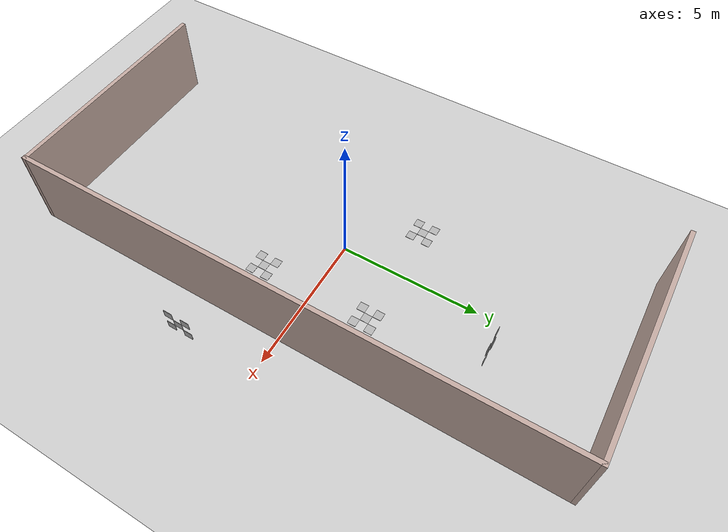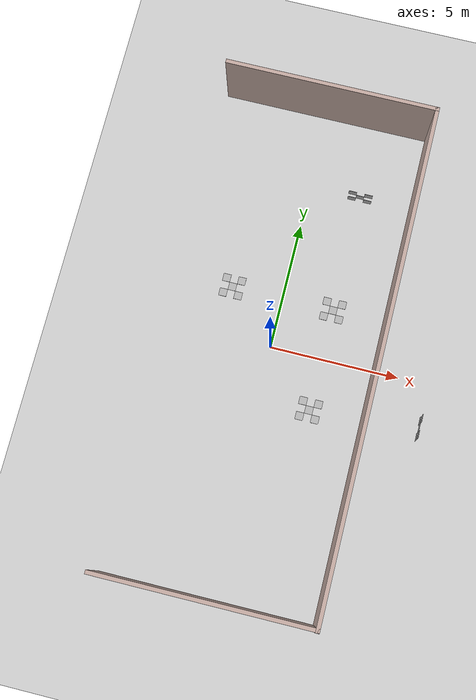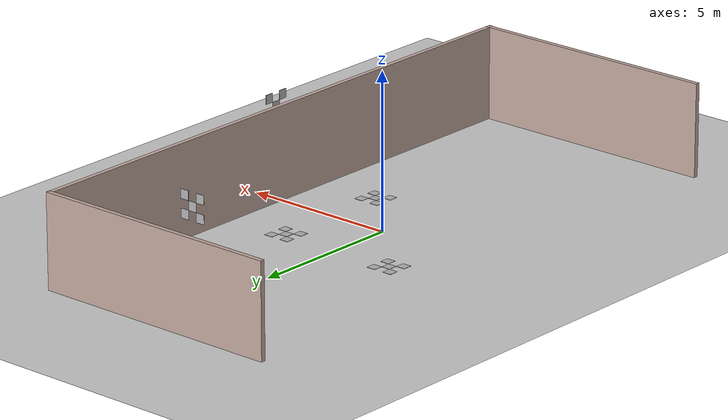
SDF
<sdf version="1.6">
 <world name="default">
  <include><uri>model://tag_bundle1</uri></include>
  <include><uri>model://tag_bundle3</uri></include>
  <include><uri>model://tag_bundle5</uri></include>
  <include><uri>model://tag_bundle2</uri></include>
  <include><uri>model://tag_bundle4</uri></include>
  <include><uri>model://tag_bundle6</uri></include>
  <plugin name="ros_interface_plugin" filename="librotors_gazebo_ros_interface_plugin.so"/>
  <spherical_coordinates>
   <surface_model>EARTH_WGS84</surface_model>
   <latitude_deg>47.3667</latitude_deg>
   <longitude_deg>8.5500</longitude_deg>
   <elevation>500.0</elevation>
   <heading_deg>0</heading_deg>
  </spherical_coordinates>
  <physics type="ode">
   <ode>
    <solver><type>quick</type><iters>1000</iters><sor>1.3</sor></solver>
    <constraints>
     <cfm>0</cfm>
     <erp>0.2</erp>
     <contact_max_correcting_vel>100</contact_max_correcting_vel>
     <contact_surface_layer>0.001</contact_surface_layer>
    </constraints>
   </ode>
   <max_step_size>0.01</max_step_size>
   <real_time_factor>1</real_time_factor>
   <real_time_update_rate>100</real_time_update_rate>
   <gravity>0 0 -9.8</gravity>
  </physics>
  <light name="sun" type="directional">
   <pose>0 0 15 0 -0 0</pose>
   <diffuse>0.8 0.8 0.8 1</diffuse>
   <specular>0.2 0.2 0.2 1</specular>
   <attenuation>
    <range>1000</range>
    <constant>0.9</constant>
    <linear>0.01</linear>
    <quadratic>0.001</quadratic>
   </attenuation>
   <direction>0.5 0.1 -0.9</direction>
  </light>
  <model name="ground_plane">
   <static>1</static>
   <link name="link">
    <collision name="collision">
     <geometry><plane><normal>0 0 1</normal><size>100 100</size></plane></geometry>
     <surface>
      <contact><collide_bitmask>65535</collide_bitmask></contact>
      <friction><ode><mu>100</mu><mu2>50</mu2></ode></friction>
     </surface>
    </collision>
    <visual name="visual">
     <cast_shadows>0</cast_shadows>
     <geometry><plane><normal>0 0 1</normal><size>100 100</size></plane></geometry>
     <material>
      <script><uri>file://media/materials/scripts/gazebo.material</uri><name>Gazebo/Grey</name></script>
     </material>
    </visual>
   </link>
  </model>
  <gravity>0 0 -9.8</gravity>
  <magnetic_field>6e-06 2.3e-05 -4.2e-05</magnetic_field>
  <atmosphere type="adiabatic"/>
  <physics name="default_physics" default="0" type="ode">
   <max_step_size>0.001</max_step_size>
   <real_time_factor>1</real_time_factor>
   <real_time_update_rate>1000</real_time_update_rate>
  </physics>
  <scene><ambient>0.4 0.4 0.4 1</ambient><background>0.7 0.7 0.7 1</background><shadows>1</shadows></scene>
  <audio><device>default</device></audio>
  <spherical_coordinates>
   <surface_model>EARTH_WGS84</surface_model>
   <latitude_deg>0</latitude_deg>
   <longitude_deg>0</longitude_deg>
   <elevation>0</elevation>
   <heading_deg>0</heading_deg>
  </spherical_coordinates>
  <model name="Room1">
   <pose>0.001 0.001 0 0 -0 0</pose>
   <link name="Wall_5">
    <collision name="Wall_5_Collision">
     <geometry><box><size>8.2375 0.15 3</size></box></geometry>
     <pose>0 0 1.5 0 -0 0</pose>
    </collision>
    <visual name="Wall_5_Visual">
     <pose>0 0 1.5 0 -0 0</pose>
     <geometry><box><size>8.2375 0.15 3</size></box></geometry>
     <material>
      <script><uri>file://media/materials/scripts/gazebo.material</uri><name>Gazebo/Grey</name></script>
      <ambient>0.760784 0.662745 0.627451 1</ambient>
     </material>
     <meta><layer>0</layer></meta>
    </visual>
    <pose>0.00159 9.72367 0 0 -0 -0.001065</pose>
   </link>
   <link name="Wall_6">
    <collision name="Wall_6_Collision">
     <geometry><box><size>19.5759 0.15 3</size></box></geometry>
     <pose>0 0 1.5 0 -0 0</pose>
    </collision>
    <visual name="Wall_6_Visual">
     <pose>0 0 1.5 0 -0 0</pose>
     <geometry><box><size>19.5759 0.15 3</size></box></geometry>
     <material>
      <script><uri>file://media/materials/scripts/gazebo.material</uri><name>Gazebo/Grey</name></script>
      <ambient>0.760784 0.662745 0.627451 1</ambient>
     </material>
     <meta><layer>0</layer></meta>
    </visual>
    <pose>4.0461 -0.021509 0 0 -0 -1.57071</pose>
   </link>
   <link name="Wall_7">
    <collision name="Wall_7_Collision">
     <geometry><box><size>8.2388 0.15 3</size></box></geometry>
     <pose>0 0 1.5 0 -0 0</pose>
    </collision>
    <visual name="Wall_7_Visual">
     <pose>0 0 1.5 0 -0 0</pose>
     <geometry><box><size>8.2388 0.15 3</size></box></geometry>
     <material>
      <script><uri>file://media/materials/scripts/gazebo.material</uri><name>Gazebo/Grey</name></script>
      <ambient>0.760784 0.662745 0.627451 1</ambient>
     </material>
     <meta><layer>0</layer></meta>
    </visual>
    <pose>0.002679 -9.71325 0 0 -0 -3.14155</pose>
   </link>
   <static>1</static>
  </model>
 </world>
</sdf>

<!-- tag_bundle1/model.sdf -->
<sdf version="1.4">

	<model name='tag_bundle1'>

		<static>True</static>

		<link name="tag_0">

			<pose>2 -2 0 0 1.5713 1.5713</pose>

			<inertial>
	        	<mass>0.1</mass>

	        	<inertia>
					<ixx>0.0166667</ixx>
					<ixy>0</ixy>
					<ixz>0</ixz>
					<iyy>0.0166667</iyy>
					<iyz>0</iyz>
					<izz>0.0166667</izz>
        		</inertia>

        		<pose frame=''>0 0 0 0 -0 0</pose>
      		</inertial>

			<pose frame=''>0 0 0 0 -0 0</pose>
			<gravity>1</gravity>
			<self_collide>0</self_collide>
			<kinematic>0</kinematic>
			<enable_wind>0</enable_wind>

			<visual name='visual_0'>
				<pose frame=''>0 0 0 0 -0 0</pose>

		        <geometry>
		        	<box>
		        	<size>0.01 0.3 0.3</size>
		        	</box>
		        </geometry>

		        <material>
		        	<lighting>0</lighting>

		        	<script>
		        		<uri>models://media/materials/scripts/Apriltag.material</uri>
		        		<name>Apriltag/id0</name>
		          	</script>

		        	<shader type='vertex'>
		        		<normal_map>__default__</normal_map>
		          	</shader>

		        	<ambient>0.3 0.3 0.3 1</ambient>
		        	<diffuse>0.7 0.7 0.7 1</diffuse>
		        	<specular>0.01 0.01 0.01 1</specular>
		        	<emissive>0 0 0 1</emissive>
		        </material>

		        <transparency>0</transparency>
		        <cast_shadows>1</cast_shadows>
			</visual>

			<collision name='collision_0'>
				<laser_retro>0</laser_retro>
        		<max_contacts>10</max_contacts>
        		<pose frame=''>0 0 0 0 -0 0</pose>

		        <geometry>
		        	<box>
		        		<size>0.01 0.3 0.3</size>
		        	</box>
		        </geometry>

		        <surface>
		        	<friction>
		            	<ode>
		            		<mu>1</mu>
		            		<mu2>1</mu2>
		            		<fdir1>0 0 0</fdir1>
		            		<slip1>0</slip1>
		            		<slip2>0</slip2>
		            	</ode>

		           		<torsional>
		            		<coefficient>1</coefficient>
	            			<patch_radius>0</patch_radius>
	            			<surface_radius>0</surface_radius>
	            			<use_patch_radius>1</use_patch_radius>

	            			<ode>
		                		<slip>0</slip>
		              		</ode>
		            	</torsional>
		          	</friction>

		        	<bounce>
		            	<restitution_coefficient>0</restitution_coefficient>
		            	<threshold>1e+06</threshold>
		        	</bounce>

		        	<contact>
		            	<collide_without_contact>0</collide_without_contact>
		            	<collide_without_contact_bitmask>1</collide_without_contact_bitmask>
		            	<collide_bitmask>1</collide_bitmask>

		            	<ode>
		            		<soft_cfm>0</soft_cfm>
		            		<soft_erp>0.2</soft_erp>
		            		<kp>1e+13</kp>
		            		<kd>1</kd>
		            		<max_vel>0.01</max_vel>
		            		<min_depth>0</min_depth>
		            	</ode>

			            <bullet>
			            	<split_impulse>1</split_impulse>
			            	<split_impulse_penetration_threshold>-0.01</split_impulse_penetration_threshold>
			            	<soft_cfm>0</soft_cfm>
			            	<soft_erp>0.2</soft_erp>
			            	<kp>1e+13</kp>
			            	<kd>1</kd>
			            </bullet>
		        	</contact>
		        </surface>
		    </collision>
		</link>

		<link name="tag_1">

			<pose>2.3 -2.3 0 0 1.5713 1.5713</pose>

			<inertial>
	        	<mass>0.1</mass>

	        	<inertia>
					<ixx>0.0166667</ixx>
					<ixy>0</ixy>
					<ixz>0</ixz>
					<iyy>0.0166667</iyy>
					<iyz>0</iyz>
					<izz>0.0166667</izz>
        		</inertia>

        		<pose frame=''>0 0 0 0 -0 0</pose>
      		</inertial>

			<pose frame=''>0 0 0 0 -0 0</pose>
			<gravity>1</gravity>
			<self_collide>0</self_collide>
			<kinematic>0</kinematic>
			<enable_wind>0</enable_wind>

 			<visual name='visual_1'>
				<pose frame=''>0 0 0 0 -0 0</pose>

		        <geometry>
		        	<box>
		        	<size>0.01 0.3 0.3</size>
		        	</box>
		        </geometry>

		        <material>
		        	<lighting>0</lighting>

		        	<script>
		        		<uri>models://media/materials/scripts/Apriltag.material</uri>
		        		<name>Apriltag/id1</name>
		          	</script>

		        	<shader type='vertex'>
		        		<normal_map>__default__</normal_map>
		          	</shader>

		        	<ambient>0.3 0.3 0.3 1</ambient>
		        	<diffuse>0.7 0.7 0.7 1</diffuse>
		        	<specular>0.01 0.01 0.01 1</specular>
		        	<emissive>0 0 0 1</emissive>
		        </material>

		        <transparency>0</transparency>
		        <cast_shadows>1</cast_shadows>
			</visual>

			<collision name='collision_1'>
				<laser_retro>0</laser_retro>
        		<max_contacts>10</max_contacts>
        		<pose frame=''>0 0 0 0 -0 0</pose>

		        <geometry>
		        	<box>
		        		<size>0.01 0.3 0.3</size>
		        	</box>
		        </geometry>

		        <surface>
		        	<friction>
		            	<ode>
		            		<mu>1</mu>
		            		<mu2>1</mu2>
		            		<fdir1>0 0 0</fdir1>
		            		<slip1>0</slip1>
		            		<slip2>0</slip2>
		            	</ode>

		           		<torsional>
		            		<coefficient>1</coefficient>
	            			<patch_radius>0</patch_radius>
	            			<surface_radius>0</surface_radius>
	            			<use_patch_radius>1</use_patch_radius>

	            			<ode>
		                		<slip>0</slip>
		              		</ode>
		            	</torsional>
		          	</friction>

		        	<bounce>
		            	<restitution_coefficient>0</restitution_coefficient>
		            	<threshold>1e+06</threshold>
		        	</bounce>

		        	<contact>
		            	<collide_without_contact>0</collide_without_contact>
		            	<collide_without_contact_bitmask>1</collide_without_contact_bitmask>
		            	<collide_bitmask>1</collide_bitmask>

		            	<ode>
		            		<soft_cfm>0</soft_cfm>
		            		<soft_erp>0.2</soft_erp>
		            		<kp>1e+13</kp>
		            		<kd>1</kd>
		            		<max_vel>0.01</max_vel>
		            		<min_depth>0</min_depth>
		            	</ode>

			            <bullet>
			            	<split_impulse>1</split_impulse>
			            	<split_impulse_penetration_threshold>-0.01</split_impulse_penetration_threshold>
			            	<soft_cfm>0</soft_cfm>
			            	<soft_erp>0.2</soft_erp>
			            	<kp>1e+13</kp>
			            	<kd>1</kd>
			            </bullet>
		        	</contact>
		        </surface>
		    </collision>
		</link>

		<link name="tag_2">

			<pose>2.3 -1.7 0 0 1.5713 1.5713</pose>

			<inertial>
	        	<mass>0.1</mass>

	        	<inertia>
					<ixx>0.0166667</ixx>
					<ixy>0</ixy>
					<ixz>0</ixz>
					<iyy>0.0166667</iyy>
					<iyz>0</iyz>
					<izz>0.0166667</izz>
        		</inertia>

        		<pose frame=''>0 0 0 0 -0 0</pose>
      		</inertial>

			<pose frame=''>0 0 0 0 -0 0</pose>
			<gravity>1</gravity>
			<self_collide>0</self_collide>
			<kinematic>0</kinematic>
			<enable_wind>0</enable_wind>

			<visual name='visual_2'>
				<pose frame=''>0 0 0 0 -0 0</pose>

		        <geometry>
		        	<box>
		        	<size>0.01 0.3 0.3</size>
		        	</box>
		        </geometry>

		        <material>
		        	<lighting>0</lighting>

		        	<script>
		        		<uri>models://media/materials/scripts/Apriltag.material</uri>
		        		<name>Apriltag/id2</name>
		          	</script>

		        	<shader type='vertex'>
		        		<normal_map>__default__</normal_map>
		          	</shader>

		        	<ambient>0.3 0.3 0.3 1</ambient>
		        	<diffuse>0.7 0.7 0.7 1</diffuse>
		        	<specular>0.01 0.01 0.01 1</specular>
		        	<emissive>0 0 0 1</emissive>
		        </material>

		        <transparency>0</transparency>
		        <cast_shadows>1</cast_shadows>
			</visual>

			<collision name='collision_2'>
				<laser_retro>0</laser_retro>
        		<max_contacts>10</max_contacts>
        		<pose frame=''>0 0 0 0 -0 0</pose>

		        <geometry>
		        	<box>
		        		<size>0.01 0.3 0.3</size>
		        	</box>
		        </geometry>

		        <surface>
		        	<friction>
		            	<ode>
		            		<mu>1</mu>
		            		<mu2>1</mu2>
		            		<fdir1>0 0 0</fdir1>
		            		<slip1>0</slip1>
		            		<slip2>0</slip2>
		            	</ode>

		           		<torsional>
		            		<coefficient>1</coefficient>
	            			<patch_radius>0</patch_radius>
	            			<surface_radius>0</surface_radius>
	            			<use_patch_radius>1</use_patch_radius>

	            			<ode>
		                		<slip>0</slip>
		              		</ode>
		            	</torsional>
		          	</friction>

		        	<bounce>
		            	<restitution_coefficient>0</restitution_coefficient>
		            	<threshold>1e+06</threshold>
		        	</bounce>

		        	<contact>
		            	<collide_without_contact>0</collide_without_contact>
		            	<collide_without_contact_bitmask>1</collide_without_contact_bitmask>
		            	<collide_bitmask>1</collide_bitmask>

		            	<ode>
		            		<soft_cfm>0</soft_cfm>
		            		<soft_erp>0.2</soft_erp>
		            		<kp>1e+13</kp>
		            		<kd>1</kd>
		            		<max_vel>0.01</max_vel>
		            		<min_depth>0</min_depth>
		            	</ode>

			            <bullet>
			            	<split_impulse>1</split_impulse>
			            	<split_impulse_penetration_threshold>-0.01</split_impulse_penetration_threshold>
			            	<soft_cfm>0</soft_cfm>
			            	<soft_erp>0.2</soft_erp>
			            	<kp>1e+13</kp>
			            	<kd>1</kd>
			            </bullet>
		        	</contact>
		        </surface>
		    </collision>
		</link>

		<link name="tag_3">

			<pose>1.7 -1.7 0 0 1.5713 1.5713</pose>

			<inertial>
	        	<mass>0.1</mass>

	        	<inertia>
					<ixx>0.0166667</ixx>
					<ixy>0</ixy>
					<ixz>0</ixz>
					<iyy>0.0166667</iyy>
					<iyz>0</iyz>
					<izz>0.0166667</izz>
        		</inertia>

        		<pose frame=''>0 0 0 0 -0 0</pose>
      		</inertial>

			<pose frame=''>0 0 0 0 -0 0</pose>
			<gravity>1</gravity>
			<self_collide>0</self_collide>
			<kinematic>0</kinematic>
			<enable_wind>0</enable_wind>

			<visual name='visual_3'>
				<pose frame=''>0 0 0 0 -0 0</pose>

		        <geometry>
		        	<box>
		        	<size>0.01 0.3 0.3</size>
		        	</box>
		        </geometry>

		        <material>
		        	<lighting>0</lighting>

		        	<script>
		        		<uri>models://media/materials/scripts/Apriltag.material</uri>
		        		<name>Apriltag/id3</name>
		          	</script>

		        	<shader type='vertex'>
		        		<normal_map>__default__</normal_map>
		          	</shader>

		        	<ambient>0.3 0.3 0.3 1</ambient>
		        	<diffuse>0.7 0.7 0.7 1</diffuse>
		        	<specular>0.01 0.01 0.01 1</specular>
		        	<emissive>0 0 0 1</emissive>
		        </material>

		        <transparency>0</transparency>
		        <cast_shadows>1</cast_shadows>
			</visual>

			<collision name='collision_3'>
				<laser_retro>0</laser_retro>
        		<max_contacts>10</max_contacts>
        		<pose frame=''>0 0 0 0 -0 0</pose>

		        <geometry>
		        	<box>
		        		<size>0.01 0.3 0.3</size>
		        	</box>
		        </geometry>

		        <surface>
		        	<friction>
		            	<ode>
		            		<mu>1</mu>
		            		<mu2>1</mu2>
		            		<fdir1>0 0 0</fdir1>
		            		<slip1>0</slip1>
		            		<slip2>0</slip2>
		            	</ode>

		           		<torsional>
		            		<coefficient>1</coefficient>
	            			<patch_radius>0</patch_radius>
	            			<surface_radius>0</surface_radius>
	            			<use_patch_radius>1</use_patch_radius>

	            			<ode>
		                		<slip>0</slip>
		              		</ode>
		            	</torsional>
		          	</friction>

		        	<bounce>
		            	<restitution_coefficient>0</restitution_coefficient>
		            	<threshold>1e+06</threshold>
		        	</bounce>

		        	<contact>
		            	<collide_without_contact>0</collide_without_contact>
		            	<collide_without_contact_bitmask>1</collide_without_contact_bitmask>
		            	<collide_bitmask>1</collide_bitmask>

		            	<ode>
		            		<soft_cfm>0</soft_cfm>
		            		<soft_erp>0.2</soft_erp>
		            		<kp>1e+13</kp>
		            		<kd>1</kd>
		            		<max_vel>0.01</max_vel>
		            		<min_depth>0</min_depth>
		            	</ode>

			            <bullet>
			            	<split_impulse>1</split_impulse>
			            	<split_impulse_penetration_threshold>-0.01</split_impulse_penetration_threshold>
			            	<soft_cfm>0</soft_cfm>
			            	<soft_erp>0.2</soft_erp>
			            	<kp>1e+13</kp>
			            	<kd>1</kd>
			            </bullet>
		        	</contact>
		        </surface>
		    </collision>
		</link>

		<link name="tag_4">

			<pose>1.7 -2.3 0 0 1.5713 1.5713</pose>

			<inertial>
	        	<mass>0.1</mass>

	        	<inertia>
					<ixx>0.0166667</ixx>
					<ixy>0</ixy>
					<ixz>0</ixz>
					<iyy>0.0166667</iyy>
					<iyz>0</iyz>
					<izz>0.0166667</izz>
        		</inertia>

        		<pose frame=''>0 0 0 0 -0 0</pose>
      		</inertial>

			<pose frame=''>0 0 0 0 -0 0</pose>
			<gravity>1</gravity>
			<self_collide>0</self_collide>
			<kinematic>0</kinematic>
			<enable_wind>0</enable_wind>

			<visual name='visual_4'>
				<pose frame=''>0 0 0 0 -0 0</pose>

		        <geometry>
		        	<box>
		        	<size>0.01 0.3 0.3</size>
		        	</box>
		        </geometry>

		        <material>
		        	<lighting>0</lighting>

		        	<script>
		        		<uri>models://media/materials/scripts/Apriltag.material</uri>
		        		<name>Apriltag/id4</name>
		          	</script>

		        	<shader type='vertex'>
		        		<normal_map>__default__</normal_map>
		          	</shader>

		        	<ambient>0.3 0.3 0.3 1</ambient>
		        	<diffuse>0.7 0.7 0.7 1</diffuse>
		        	<specular>0.01 0.01 0.01 1</specular>
		        	<emissive>0 0 0 1</emissive>
		        </material>

		        <transparency>0</transparency>
		        <cast_shadows>1</cast_shadows>
			</visual>

			<collision name='collision_4'>
				<laser_retro>0</laser_retro>
        		<max_contacts>10</max_contacts>
        		<pose frame=''>0 0 0 0 -0 0</pose>

		        <geometry>
		        	<box>
		        		<size>0.01 0.3 0.3</size>
		        	</box>
		        </geometry>

		        <surface>
		        	<friction>
		            	<ode>
		            		<mu>1</mu>
		            		<mu2>1</mu2>
		            		<fdir1>0 0 0</fdir1>
		            		<slip1>0</slip1>
		            		<slip2>0</slip2>
		            	</ode>

		           		<torsional>
		            		<coefficient>1</coefficient>
	            			<patch_radius>0</patch_radius>
	            			<surface_radius>0</surface_radius>
	            			<use_patch_radius>1</use_patch_radius>

	            			<ode>
		                		<slip>0</slip>
		              		</ode>
		            	</torsional>
		          	</friction>

		        	<bounce>
		            	<restitution_coefficient>0</restitution_coefficient>
		            	<threshold>1e+06</threshold>
		        	</bounce>

		        	<contact>
		            	<collide_without_contact>0</collide_without_contact>
		            	<collide_without_contact_bitmask>1</collide_without_contact_bitmask>
		            	<collide_bitmask>1</collide_bitmask>

		            	<ode>
		            		<soft_cfm>0</soft_cfm>
		            		<soft_erp>0.2</soft_erp>
		            		<kp>1e+13</kp>
		            		<kd>1</kd>
		            		<max_vel>0.01</max_vel>
		            		<min_depth>0</min_depth>
		            	</ode>

			            <bullet>
			            	<split_impulse>1</split_impulse>
			            	<split_impulse_penetration_threshold>-0.01</split_impulse_penetration_threshold>
			            	<soft_cfm>0</soft_cfm>
			            	<soft_erp>0.2</soft_erp>
			            	<kp>1e+13</kp>
			            	<kd>1</kd>
			            </bullet>
		        	</contact>
		        </surface>
		    </collision>
		</link>

		<joint name = "joint_1" type="fixed">
			<axis xyz="0 0 0" />
			<parent link="tag_0" />
			<child link="tag_1" />
	    </joint>

	    <joint name = "joint_2" type="fixed">
			<axis xyz="0 0 0" />
			<parent link="tag_0" />
			<child link="tag_2" />
	    </joint>

	    <joint name = "joint_3" type="fixed">
			<axis xyz="0 0 0" />
			<parent link="tag_0" />
			<child link="tag_3" />
	    </joint>

	    <joint name = "joint_4" type="fixed">
			<axis xyz="0 0 0" />
			<parent link="tag_0" />
			<child link="tag_4" />
	    </joint>

	</model>

</sdf>

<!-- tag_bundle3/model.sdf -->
<sdf version="1.4">

	<model name='tag_bundle3'>

		<static>True</static>

		<link name="tag_10">

			<pose>2 2 0 0 1.5713 1.5713</pose>

			<inertial>
	        	<mass>0.1</mass>

	        	<inertia>
					<ixx>0.0166667</ixx>
					<ixy>0</ixy>
					<ixz>0</ixz>
					<iyy>0.0166667</iyy>
					<iyz>0</iyz>
					<izz>0.0166667</izz>
        		</inertia>

        		<pose frame=''>0 0 0 0 -0 0</pose>
      		</inertial>

			<pose frame=''>0 0 0 0 -0 0</pose>
			<gravity>1</gravity>
			<self_collide>0</self_collide>
			<kinematic>0</kinematic>
			<enable_wind>0</enable_wind>

			<visual name='visual_10'>
				<pose frame=''>0 0 0 0 -0 0</pose>

		        <geometry>
		        	<box>
		        	<size>0.01 0.3 0.3</size>
		        	</box>
		        </geometry>

		        <material>
		        	<lighting>0</lighting>

		        	<script>
		        		<uri>models://media/materials/scripts/Apriltag.material</uri>
		        		<name>Apriltag/id10</name>
		          	</script>

		        	<shader type='vertex'>
		        		<normal_map>__default__</normal_map>
		          	</shader>

		        	<ambient>0.3 0.3 0.3 1</ambient>
		        	<diffuse>0.7 0.7 0.7 1</diffuse>
		        	<specular>0.01 0.01 0.01 1</specular>
		        	<emissive>0 0 0 1</emissive>
		        </material>

		        <transparency>0</transparency>
		        <cast_shadows>1</cast_shadows>
			</visual>

			<collision name='collision_10'>
				<laser_retro>0</laser_retro>
        		<max_contacts>10</max_contacts>
        		<pose frame=''>0 0 0 0 -0 0</pose>

		        <geometry>
		        	<box>
		        		<size>0.01 0.3 0.3</size>
		        	</box>
		        </geometry>

		        <surface>
		        	<friction>
		            	<ode>
		            		<mu>1</mu>
		            		<mu2>1</mu2>
		            		<fdir1>0 0 0</fdir1>
		            		<slip1>0</slip1>
		            		<slip2>0</slip2>
		            	</ode>

		           		<torsional>
		            		<coefficient>1</coefficient>
	            			<patch_radius>0</patch_radius>
	            			<surface_radius>0</surface_radius>
	            			<use_patch_radius>1</use_patch_radius>

	            			<ode>
		                		<slip>0</slip>
		              		</ode>
		            	</torsional>
		          	</friction>

		        	<bounce>
		            	<restitution_coefficient>0</restitution_coefficient>
		            	<threshold>1e+06</threshold>
		        	</bounce>

		        	<contact>
		            	<collide_without_contact>0</collide_without_contact>
		            	<collide_without_contact_bitmask>1</collide_without_contact_bitmask>
		            	<collide_bitmask>1</collide_bitmask>

		            	<ode>
		            		<soft_cfm>0</soft_cfm>
		            		<soft_erp>0.2</soft_erp>
		            		<kp>1e+13</kp>
		            		<kd>1</kd>
		            		<max_vel>0.01</max_vel>
		            		<min_depth>0</min_depth>
		            	</ode>

			            <bullet>
			            	<split_impulse>1</split_impulse>
			            	<split_impulse_penetration_threshold>-0.01</split_impulse_penetration_threshold>
			            	<soft_cfm>0</soft_cfm>
			            	<soft_erp>0.2</soft_erp>
			            	<kp>1e+13</kp>
			            	<kd>1</kd>
			            </bullet>
		        	</contact>
		        </surface>
		    </collision>
		</link>

		<link name="tag_11">

			<pose>2.3 1.7 0 0 1.5713 1.5713</pose>

			<inertial>
	        	<mass>0.1</mass>

	        	<inertia>
					<ixx>0.0166667</ixx>
					<ixy>0</ixy>
					<ixz>0</ixz>
					<iyy>0.0166667</iyy>
					<iyz>0</iyz>
					<izz>0.0166667</izz>
        		</inertia>

        		<pose frame=''>0 0 0 0 -0 0</pose>
      		</inertial>

			<pose frame=''>0 0 0 0 -0 0</pose>
			<gravity>1</gravity>
			<self_collide>0</self_collide>
			<kinematic>0</kinematic>
			<enable_wind>0</enable_wind>

 			<visual name='visual_11'>
				<pose frame=''>0 0 0 0 -0 0</pose>

		        <geometry>
		        	<box>
		        	<size>0.01 0.3 0.3</size>
		        	</box>
		        </geometry>

		        <material>
		        	<lighting>0</lighting>

		        	<script>
		        		<uri>models://media/materials/scripts/Apriltag.material</uri>
		        		<name>Apriltag/id11</name>
		          	</script>

		        	<shader type='vertex'>
		        		<normal_map>__default__</normal_map>
		          	</shader>

		        	<ambient>0.3 0.3 0.3 1</ambient>
		        	<diffuse>0.7 0.7 0.7 1</diffuse>
		        	<specular>0.01 0.01 0.01 1</specular>
		        	<emissive>0 0 0 1</emissive>
		        </material>

		        <transparency>0</transparency>
		        <cast_shadows>1</cast_shadows>
			</visual>

			<collision name='collision_11'>
				<laser_retro>0</laser_retro>
        		<max_contacts>10</max_contacts>
        		<pose frame=''>0 0 0 0 -0 0</pose>

		        <geometry>
		        	<box>
		        		<size>0.01 0.3 0.3</size>
		        	</box>
		        </geometry>

		        <surface>
		        	<friction>
		            	<ode>
		            		<mu>1</mu>
		            		<mu2>1</mu2>
		            		<fdir1>0 0 0</fdir1>
		            		<slip1>0</slip1>
		            		<slip2>0</slip2>
		            	</ode>

		           		<torsional>
		            		<coefficient>1</coefficient>
	            			<patch_radius>0</patch_radius>
	            			<surface_radius>0</surface_radius>
	            			<use_patch_radius>1</use_patch_radius>

	            			<ode>
		                		<slip>0</slip>
		              		</ode>
		            	</torsional>
		          	</friction>

		        	<bounce>
		            	<restitution_coefficient>0</restitution_coefficient>
		            	<threshold>1e+06</threshold>
		        	</bounce>

		        	<contact>
		            	<collide_without_contact>0</collide_without_contact>
		            	<collide_without_contact_bitmask>1</collide_without_contact_bitmask>
		            	<collide_bitmask>1</collide_bitmask>

		            	<ode>
		            		<soft_cfm>0</soft_cfm>
		            		<soft_erp>0.2</soft_erp>
		            		<kp>1e+13</kp>
		            		<kd>1</kd>
		            		<max_vel>0.01</max_vel>
		            		<min_depth>0</min_depth>
		            	</ode>

			            <bullet>
			            	<split_impulse>1</split_impulse>
			            	<split_impulse_penetration_threshold>-0.01</split_impulse_penetration_threshold>
			            	<soft_cfm>0</soft_cfm>
			            	<soft_erp>0.2</soft_erp>
			            	<kp>1e+13</kp>
			            	<kd>1</kd>
			            </bullet>
		        	</contact>
		        </surface>
		    </collision>
		</link>

		<link name="tag_12">

			<pose>2.3 2.3 0 0 1.5713 1.5713</pose>

			<inertial>
	        	<mass>0.1</mass>

	        	<inertia>
					<ixx>0.0166667</ixx>
					<ixy>0</ixy>
					<ixz>0</ixz>
					<iyy>0.0166667</iyy>
					<iyz>0</iyz>
					<izz>0.0166667</izz>
        		</inertia>

        		<pose frame=''>0 0 0 0 -0 0</pose>
      		</inertial>

			<pose frame=''>0 0 0 0 -0 0</pose>
			<gravity>1</gravity>
			<self_collide>0</self_collide>
			<kinematic>0</kinematic>
			<enable_wind>0</enable_wind>

			<visual name='visual_12'>
				<pose frame=''>0 0 0 0 -0 0</pose>

		        <geometry>
		        	<box>
		        	<size>0.01 0.3 0.3</size>
		        	</box>
		        </geometry>

		        <material>
		        	<lighting>0</lighting>

		        	<script>
		        		<uri>models://media/materials/scripts/Apriltag.material</uri>
		        		<name>Apriltag/id12</name>
		          	</script>

		        	<shader type='vertex'>
		        		<normal_map>__default__</normal_map>
		          	</shader>

		        	<ambient>0.3 0.3 0.3 1</ambient>
		        	<diffuse>0.7 0.7 0.7 1</diffuse>
		        	<specular>0.01 0.01 0.01 1</specular>
		        	<emissive>0 0 0 1</emissive>
		        </material>

		        <transparency>0</transparency>
		        <cast_shadows>1</cast_shadows>
			</visual>

			<collision name='collision_12'>
				<laser_retro>0</laser_retro>
        		<max_contacts>10</max_contacts>
        		<pose frame=''>0 0 0 0 -0 0</pose>

		        <geometry>
		        	<box>
		        		<size>0.01 0.3 0.3</size>
		        	</box>
		        </geometry>

		        <surface>
		        	<friction>
		            	<ode>
		            		<mu>1</mu>
		            		<mu2>1</mu2>
		            		<fdir1>0 0 0</fdir1>
		            		<slip1>0</slip1>
		            		<slip2>0</slip2>
		            	</ode>

		           		<torsional>
		            		<coefficient>1</coefficient>
	            			<patch_radius>0</patch_radius>
	            			<surface_radius>0</surface_radius>
	            			<use_patch_radius>1</use_patch_radius>

	            			<ode>
		                		<slip>0</slip>
		              		</ode>
		            	</torsional>
		          	</friction>

		        	<bounce>
		            	<restitution_coefficient>0</restitution_coefficient>
		            	<threshold>1e+06</threshold>
		        	</bounce>

		        	<contact>
		            	<collide_without_contact>0</collide_without_contact>
		            	<collide_without_contact_bitmask>1</collide_without_contact_bitmask>
		            	<collide_bitmask>1</collide_bitmask>

		            	<ode>
		            		<soft_cfm>0</soft_cfm>
		            		<soft_erp>0.2</soft_erp>
		            		<kp>1e+13</kp>
		            		<kd>1</kd>
		            		<max_vel>0.01</max_vel>
		            		<min_depth>0</min_depth>
		            	</ode>

			            <bullet>
			            	<split_impulse>1</split_impulse>
			            	<split_impulse_penetration_threshold>-0.01</split_impulse_penetration_threshold>
			            	<soft_cfm>0</soft_cfm>
			            	<soft_erp>0.2</soft_erp>
			            	<kp>1e+13</kp>
			            	<kd>1</kd>
			            </bullet>
		        	</contact>
		        </surface>
		    </collision>
		</link>

		<link name="tag_13">

			<pose>1.7 2.3 0 0 1.5713 1.5713</pose>

			<inertial>
	        	<mass>0.1</mass>

	        	<inertia>
					<ixx>0.0166667</ixx>
					<ixy>0</ixy>
					<ixz>0</ixz>
					<iyy>0.0166667</iyy>
					<iyz>0</iyz>
					<izz>0.0166667</izz>
        		</inertia>

        		<pose frame=''>0 0 0 0 -0 0</pose>
      		</inertial>

			<pose frame=''>0 0 0 0 -0 0</pose>
			<gravity>1</gravity>
			<self_collide>0</self_collide>
			<kinematic>0</kinematic>
			<enable_wind>0</enable_wind>

			<visual name='visual_13'>
				<pose frame=''>0 0 0 0 -0 0</pose>

		        <geometry>
		        	<box>
		        	<size>0.01 0.3 0.3</size>
		        	</box>
		        </geometry>

		        <material>
		        	<lighting>0</lighting>

		        	<script>
		        		<uri>models://media/materials/scripts/Apriltag.material</uri>
		        		<name>Apriltag/id13</name>
		          	</script>

		        	<shader type='vertex'>
		        		<normal_map>__default__</normal_map>
		          	</shader>

		        	<ambient>0.3 0.3 0.3 1</ambient>
		        	<diffuse>0.7 0.7 0.7 1</diffuse>
		        	<specular>0.01 0.01 0.01 1</specular>
		        	<emissive>0 0 0 1</emissive>
		        </material>

		        <transparency>0</transparency>
		        <cast_shadows>1</cast_shadows>
			</visual>

			<collision name='collision_13'>
				<laser_retro>0</laser_retro>
        		<max_contacts>10</max_contacts>
        		<pose frame=''>0 0 0 0 -0 0</pose>

		        <geometry>
		        	<box>
		        		<size>0.01 0.3 0.3</size>
		        	</box>
		        </geometry>

		        <surface>
		        	<friction>
		            	<ode>
		            		<mu>1</mu>
		            		<mu2>1</mu2>
		            		<fdir1>0 0 0</fdir1>
		            		<slip1>0</slip1>
		            		<slip2>0</slip2>
		            	</ode>

		           		<torsional>
		            		<coefficient>1</coefficient>
	            			<patch_radius>0</patch_radius>
	            			<surface_radius>0</surface_radius>
	            			<use_patch_radius>1</use_patch_radius>

	            			<ode>
		                		<slip>0</slip>
		              		</ode>
		            	</torsional>
		          	</friction>

		        	<bounce>
		            	<restitution_coefficient>0</restitution_coefficient>
		            	<threshold>1e+06</threshold>
		        	</bounce>

		        	<contact>
		            	<collide_without_contact>0</collide_without_contact>
		            	<collide_without_contact_bitmask>1</collide_without_contact_bitmask>
		            	<collide_bitmask>1</collide_bitmask>

		            	<ode>
		            		<soft_cfm>0</soft_cfm>
		            		<soft_erp>0.2</soft_erp>
		            		<kp>1e+13</kp>
		            		<kd>1</kd>
		            		<max_vel>0.01</max_vel>
		            		<min_depth>0</min_depth>
		            	</ode>

			            <bullet>
			            	<split_impulse>1</split_impulse>
			            	<split_impulse_penetration_threshold>-0.01</split_impulse_penetration_threshold>
			            	<soft_cfm>0</soft_cfm>
			            	<soft_erp>0.2</soft_erp>
			            	<kp>1e+13</kp>
			            	<kd>1</kd>
			            </bullet>
		        	</contact>
		        </surface>
		    </collision>
		</link>

		<link name="tag_14">

			<pose>1.7 1.7 0 0 1.5713 1.5713</pose>

			<inertial>
	        	<mass>0.1</mass>

	        	<inertia>
					<ixx>0.0166667</ixx>
					<ixy>0</ixy>
					<ixz>0</ixz>
					<iyy>0.0166667</iyy>
					<iyz>0</iyz>
					<izz>0.0166667</izz>
        		</inertia>

        		<pose frame=''>0 0 0 0 -0 0</pose>
      		</inertial>

			<pose frame=''>0 0 0 0 -0 0</pose>
			<gravity>1</gravity>
			<self_collide>0</self_collide>
			<kinematic>0</kinematic>
			<enable_wind>0</enable_wind>

			<visual name='visual_14'>
				<pose frame=''>0 0 0 0 -0 0</pose>

		        <geometry>
		        	<box>
		        	<size>0.01 0.3 0.3</size>
		        	</box>
		        </geometry>

		        <material>
		        	<lighting>0</lighting>

		        	<script>
		        		<uri>models://media/materials/scripts/Apriltag.material</uri>
		        		<name>Apriltag/id14</name>
		          	</script>

		        	<shader type='vertex'>
		        		<normal_map>__default__</normal_map>
		          	</shader>

		        	<ambient>0.3 0.3 0.3 1</ambient>
		        	<diffuse>0.7 0.7 0.7 1</diffuse>
		        	<specular>0.01 0.01 0.01 1</specular>
		        	<emissive>0 0 0 1</emissive>
		        </material>

		        <transparency>0</transparency>
		        <cast_shadows>1</cast_shadows>
			</visual>

			<collision name='collision_14'>
				<laser_retro>0</laser_retro>
        		<max_contacts>10</max_contacts>
        		<pose frame=''>0 0 0 0 -0 0</pose>

		        <geometry>
		        	<box>
		        		<size>0.01 0.3 0.3</size>
		        	</box>
		        </geometry>

		        <surface>
		        	<friction>
		            	<ode>
		            		<mu>1</mu>
		            		<mu2>1</mu2>
		            		<fdir1>0 0 0</fdir1>
		            		<slip1>0</slip1>
		            		<slip2>0</slip2>
		            	</ode>

		           		<torsional>
		            		<coefficient>1</coefficient>
	            			<patch_radius>0</patch_radius>
	            			<surface_radius>0</surface_radius>
	            			<use_patch_radius>1</use_patch_radius>

	            			<ode>
		                		<slip>0</slip>
		              		</ode>
		            	</torsional>
		          	</friction>

		        	<bounce>
		            	<restitution_coefficient>0</restitution_coefficient>
		            	<threshold>1e+06</threshold>
		        	</bounce>

		        	<contact>
		            	<collide_without_contact>0</collide_without_contact>
		            	<collide_without_contact_bitmask>1</collide_without_contact_bitmask>
		            	<collide_bitmask>1</collide_bitmask>

		            	<ode>
		            		<soft_cfm>0</soft_cfm>
		            		<soft_erp>0.2</soft_erp>
		            		<kp>1e+13</kp>
		            		<kd>1</kd>
		            		<max_vel>0.01</max_vel>
		            		<min_depth>0</min_depth>
		            	</ode>

			            <bullet>
			            	<split_impulse>1</split_impulse>
			            	<split_impulse_penetration_threshold>-0.01</split_impulse_penetration_threshold>
			            	<soft_cfm>0</soft_cfm>
			            	<soft_erp>0.2</soft_erp>
			            	<kp>1e+13</kp>
			            	<kd>1</kd>
			            </bullet>
		        	</contact>
		        </surface>
		    </collision>
		</link>

		<joint name = "joint_1" type="fixed">
			<axis xyz="0 0 0" />
			<parent link="tag_10" />
			<child link="tag_11" />
	    </joint>

	    <joint name = "joint_2" type="fixed">
			<axis xyz="0 0 0" />
			<parent link="tag_10" />
			<child link="tag_12" />
	    </joint>

	    <joint name = "joint_3" type="fixed">
			<axis xyz="0 0 0" />
			<parent link="tag_10" />
			<child link="tag_13" />
	    </joint>

	    <joint name = "joint_4" type="fixed">
			<axis xyz="0 0 0" />
			<parent link="tag_10" />
			<child link="tag_14" />
	    </joint>

	</model>

</sdf>

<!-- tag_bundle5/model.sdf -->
<sdf version="1.4">

	<model name='tag_bundle5'>

		<static>True</static>

		<link name="tag_20">

			<pose>-2 2 0 0 1.5713 1.5713</pose>

			<inertial>
	        	<mass>0.1</mass>

	        	<inertia>
					<ixx>0.0166667</ixx>
					<ixy>0</ixy>
					<ixz>0</ixz>
					<iyy>0.0166667</iyy>
					<iyz>0</iyz>
					<izz>0.0166667</izz>
        		</inertia>

        		<pose frame=''>0 0 0 0 -0 0</pose>
      		</inertial>

			<pose frame=''>0 0 0 0 -0 0</pose>
			<gravity>1</gravity>
			<self_collide>0</self_collide>
			<kinematic>0</kinematic>
			<enable_wind>0</enable_wind>

			<visual name='visual_20'>
				<pose frame=''>0 0 0 0 -0 0</pose>

		        <geometry>
		        	<box>
		        	<size>0.01 0.3 0.3</size>
		        	</box>
		        </geometry>

		        <material>
		        	<lighting>0</lighting>

		        	<script>
		        		<uri>models://media/materials/scripts/Apriltag.material</uri>
		        		<name>Apriltag/id20</name>
		          	</script>

		        	<shader type='vertex'>
		        		<normal_map>__default__</normal_map>
		          	</shader>

		        	<ambient>0.3 0.3 0.3 1</ambient>
		        	<diffuse>0.7 0.7 0.7 1</diffuse>
		        	<specular>0.01 0.01 0.01 1</specular>
		        	<emissive>0 0 0 1</emissive>
		        </material>

		        <transparency>0</transparency>
		        <cast_shadows>1</cast_shadows>
			</visual>

			<collision name='collision_20'>
				<laser_retro>0</laser_retro>
        		<max_contacts>10</max_contacts>
        		<pose frame=''>0 0 0 0 -0 0</pose>

		        <geometry>
		        	<box>
		        		<size>0.01 0.3 0.3</size>
		        	</box>
		        </geometry>

		        <surface>
		        	<friction>
		            	<ode>
		            		<mu>1</mu>
		            		<mu2>1</mu2>
		            		<fdir1>0 0 0</fdir1>
		            		<slip1>0</slip1>
		            		<slip2>0</slip2>
		            	</ode>

		           		<torsional>
		            		<coefficient>1</coefficient>
	            			<patch_radius>0</patch_radius>
	            			<surface_radius>0</surface_radius>
	            			<use_patch_radius>1</use_patch_radius>

	            			<ode>
		                		<slip>0</slip>
		              		</ode>
		            	</torsional>
		          	</friction>

		        	<bounce>
		            	<restitution_coefficient>0</restitution_coefficient>
		            	<threshold>1e+06</threshold>
		        	</bounce>

		        	<contact>
		            	<collide_without_contact>0</collide_without_contact>
		            	<collide_without_contact_bitmask>1</collide_without_contact_bitmask>
		            	<collide_bitmask>1</collide_bitmask>

		            	<ode>
		            		<soft_cfm>0</soft_cfm>
		            		<soft_erp>0.2</soft_erp>
		            		<kp>1e+13</kp>
		            		<kd>1</kd>
		            		<max_vel>0.01</max_vel>
		            		<min_depth>0</min_depth>
		            	</ode>

			            <bullet>
			            	<split_impulse>1</split_impulse>
			            	<split_impulse_penetration_threshold>-0.01</split_impulse_penetration_threshold>
			            	<soft_cfm>0</soft_cfm>
			            	<soft_erp>0.2</soft_erp>
			            	<kp>1e+13</kp>
			            	<kd>1</kd>
			            </bullet>
		        	</contact>
		        </surface>
		    </collision>
		</link>

		<link name="tag_21">

			<pose>-1.7 1.7 0 0 1.5713 1.5713</pose>

			<inertial>
	        	<mass>0.1</mass>

	        	<inertia>
					<ixx>0.0166667</ixx>
					<ixy>0</ixy>
					<ixz>0</ixz>
					<iyy>0.0166667</iyy>
					<iyz>0</iyz>
					<izz>0.0166667</izz>
        		</inertia>

        		<pose frame=''>0 0 0 0 -0 0</pose>
      		</inertial>

			<pose frame=''>0 0 0 0 -0 0</pose>
			<gravity>1</gravity>
			<self_collide>0</self_collide>
			<kinematic>0</kinematic>
			<enable_wind>0</enable_wind>

 			<visual name='visual_21'>
				<pose frame=''>0 0 0 0 -0 0</pose>

		        <geometry>
		        	<box>
		        	<size>0.01 0.3 0.3</size>
		        	</box>
		        </geometry>

		        <material>
		        	<lighting>0</lighting>

		        	<script>
		        		<uri>models://media/materials/scripts/Apriltag.material</uri>
		        		<name>Apriltag/id21</name>
		          	</script>

		        	<shader type='vertex'>
		        		<normal_map>__default__</normal_map>
		          	</shader>

		        	<ambient>0.3 0.3 0.3 1</ambient>
		        	<diffuse>0.7 0.7 0.7 1</diffuse>
		        	<specular>0.01 0.01 0.01 1</specular>
		        	<emissive>0 0 0 1</emissive>
		        </material>

		        <transparency>0</transparency>
		        <cast_shadows>1</cast_shadows>
			</visual>

			<collision name='collision_21'>
				<laser_retro>0</laser_retro>
        		<max_contacts>10</max_contacts>
        		<pose frame=''>0 0 0 0 -0 0</pose>

		        <geometry>
		        	<box>
		        		<size>0.01 0.3 0.3</size>
		        	</box>
		        </geometry>

		        <surface>
		        	<friction>
		            	<ode>
		            		<mu>1</mu>
		            		<mu2>1</mu2>
		            		<fdir1>0 0 0</fdir1>
		            		<slip1>0</slip1>
		            		<slip2>0</slip2>
		            	</ode>

		           		<torsional>
		            		<coefficient>1</coefficient>
	            			<patch_radius>0</patch_radius>
	            			<surface_radius>0</surface_radius>
	            			<use_patch_radius>1</use_patch_radius>

	            			<ode>
		                		<slip>0</slip>
		              		</ode>
		            	</torsional>
		          	</friction>

		        	<bounce>
		            	<restitution_coefficient>0</restitution_coefficient>
		            	<threshold>1e+06</threshold>
		        	</bounce>

		        	<contact>
		            	<collide_without_contact>0</collide_without_contact>
		            	<collide_without_contact_bitmask>1</collide_without_contact_bitmask>
		            	<collide_bitmask>1</collide_bitmask>

		            	<ode>
		            		<soft_cfm>0</soft_cfm>
		            		<soft_erp>0.2</soft_erp>
		            		<kp>1e+13</kp>
		            		<kd>1</kd>
		            		<max_vel>0.01</max_vel>
		            		<min_depth>0</min_depth>
		            	</ode>

			            <bullet>
			            	<split_impulse>1</split_impulse>
			            	<split_impulse_penetration_threshold>-0.01</split_impulse_penetration_threshold>
			            	<soft_cfm>0</soft_cfm>
			            	<soft_erp>0.2</soft_erp>
			            	<kp>1e+13</kp>
			            	<kd>1</kd>
			            </bullet>
		        	</contact>
		        </surface>
		    </collision>
		</link>

		<link name="tag_22">

			<pose>-1.7 2.3 0 0 1.5713 1.5713</pose>

			<inertial>
	        	<mass>0.1</mass>

	        	<inertia>
					<ixx>0.0166667</ixx>
					<ixy>0</ixy>
					<ixz>0</ixz>
					<iyy>0.0166667</iyy>
					<iyz>0</iyz>
					<izz>0.0166667</izz>
        		</inertia>

        		<pose frame=''>0 0 0 0 -0 0</pose>
      		</inertial>

			<pose frame=''>0 0 0 0 -0 0</pose>
			<gravity>1</gravity>
			<self_collide>0</self_collide>
			<kinematic>0</kinematic>
			<enable_wind>0</enable_wind>

			<visual name='visual_22'>
				<pose frame=''>0 0 0 0 -0 0</pose>

		        <geometry>
		        	<box>
		        	<size>0.01 0.3 0.3</size>
		        	</box>
		        </geometry>

		        <material>
		        	<lighting>0</lighting>

		        	<script>
		        		<uri>models://media/materials/scripts/Apriltag.material</uri>
		        		<name>Apriltag/id22</name>
		          	</script>

		        	<shader type='vertex'>
		        		<normal_map>__default__</normal_map>
		          	</shader>

		        	<ambient>0.3 0.3 0.3 1</ambient>
		        	<diffuse>0.7 0.7 0.7 1</diffuse>
		        	<specular>0.01 0.01 0.01 1</specular>
		        	<emissive>0 0 0 1</emissive>
		        </material>

		        <transparency>0</transparency>
		        <cast_shadows>1</cast_shadows>
			</visual>

			<collision name='collision_22'>
				<laser_retro>0</laser_retro>
        		<max_contacts>10</max_contacts>
        		<pose frame=''>0 0 0 0 -0 0</pose>

		        <geometry>
		        	<box>
		        		<size>0.01 0.3 0.3</size>
		        	</box>
		        </geometry>

		        <surface>
		        	<friction>
		            	<ode>
		            		<mu>1</mu>
		            		<mu2>1</mu2>
		            		<fdir1>0 0 0</fdir1>
		            		<slip1>0</slip1>
		            		<slip2>0</slip2>
		            	</ode>

		           		<torsional>
		            		<coefficient>1</coefficient>
	            			<patch_radius>0</patch_radius>
	            			<surface_radius>0</surface_radius>
	            			<use_patch_radius>1</use_patch_radius>

	            			<ode>
		                		<slip>0</slip>
		              		</ode>
		            	</torsional>
		          	</friction>

		        	<bounce>
		            	<restitution_coefficient>0</restitution_coefficient>
		            	<threshold>1e+06</threshold>
		        	</bounce>

		        	<contact>
		            	<collide_without_contact>0</collide_without_contact>
		            	<collide_without_contact_bitmask>1</collide_without_contact_bitmask>
		            	<collide_bitmask>1</collide_bitmask>

		            	<ode>
		            		<soft_cfm>0</soft_cfm>
		            		<soft_erp>0.2</soft_erp>
		            		<kp>1e+13</kp>
		            		<kd>1</kd>
		            		<max_vel>0.01</max_vel>
		            		<min_depth>0</min_depth>
		            	</ode>

			            <bullet>
			            	<split_impulse>1</split_impulse>
			            	<split_impulse_penetration_threshold>-0.01</split_impulse_penetration_threshold>
			            	<soft_cfm>0</soft_cfm>
			            	<soft_erp>0.2</soft_erp>
			            	<kp>1e+13</kp>
			            	<kd>1</kd>
			            </bullet>
		        	</contact>
		        </surface>
		    </collision>
		</link>

		<link name="tag_23">

			<pose>-2.3 2.3 0 0 1.5713 1.5713</pose>

			<inertial>
	        	<mass>0.1</mass>

	        	<inertia>
					<ixx>0.0166667</ixx>
					<ixy>0</ixy>
					<ixz>0</ixz>
					<iyy>0.0166667</iyy>
					<iyz>0</iyz>
					<izz>0.0166667</izz>
        		</inertia>

        		<pose frame=''>0 0 0 0 -0 0</pose>
      		</inertial>

			<pose frame=''>0 0 0 0 -0 0</pose>
			<gravity>1</gravity>
			<self_collide>0</self_collide>
			<kinematic>0</kinematic>
			<enable_wind>0</enable_wind>

			<visual name='visual_23'>
				<pose frame=''>0 0 0 0 -0 0</pose>

		        <geometry>
		        	<box>
		        	<size>0.01 0.3 0.3</size>
		        	</box>
		        </geometry>

		        <material>
		        	<lighting>0</lighting>

		        	<script>
		        		<uri>models://media/materials/scripts/Apriltag.material</uri>
		        		<name>Apriltag/id23</name>
		          	</script>

		        	<shader type='vertex'>
		        		<normal_map>__default__</normal_map>
		          	</shader>

		        	<ambient>0.3 0.3 0.3 1</ambient>
		        	<diffuse>0.7 0.7 0.7 1</diffuse>
		        	<specular>0.01 0.01 0.01 1</specular>
		        	<emissive>0 0 0 1</emissive>
		        </material>

		        <transparency>0</transparency>
		        <cast_shadows>1</cast_shadows>
			</visual>

			<collision name='collision_23'>
				<laser_retro>0</laser_retro>
        		<max_contacts>10</max_contacts>
        		<pose frame=''>0 0 0 0 -0 0</pose>

		        <geometry>
		        	<box>
		        		<size>0.01 0.3 0.3</size>
		        	</box>
		        </geometry>

		        <surface>
		        	<friction>
		            	<ode>
		            		<mu>1</mu>
		            		<mu2>1</mu2>
		            		<fdir1>0 0 0</fdir1>
		            		<slip1>0</slip1>
		            		<slip2>0</slip2>
		            	</ode>

		           		<torsional>
		            		<coefficient>1</coefficient>
	            			<patch_radius>0</patch_radius>
	            			<surface_radius>0</surface_radius>
	            			<use_patch_radius>1</use_patch_radius>

	            			<ode>
		                		<slip>0</slip>
		              		</ode>
		            	</torsional>
		          	</friction>

		        	<bounce>
		            	<restitution_coefficient>0</restitution_coefficient>
		            	<threshold>1e+06</threshold>
		        	</bounce>

		        	<contact>
		            	<collide_without_contact>0</collide_without_contact>
		            	<collide_without_contact_bitmask>1</collide_without_contact_bitmask>
		            	<collide_bitmask>1</collide_bitmask>

		            	<ode>
		            		<soft_cfm>0</soft_cfm>
		            		<soft_erp>0.2</soft_erp>
		            		<kp>1e+13</kp>
		            		<kd>1</kd>
		            		<max_vel>0.01</max_vel>
		            		<min_depth>0</min_depth>
		            	</ode>

			            <bullet>
			            	<split_impulse>1</split_impulse>
			            	<split_impulse_penetration_threshold>-0.01</split_impulse_penetration_threshold>
			            	<soft_cfm>0</soft_cfm>
			            	<soft_erp>0.2</soft_erp>
			            	<kp>1e+13</kp>
			            	<kd>1</kd>
			            </bullet>
		        	</contact>
		        </surface>
		    </collision>
		</link>

		<link name="tag_24">

			<pose>-2.3 1.7 0 0 1.5713 1.5713</pose>

			<inertial>
	        	<mass>0.1</mass>

	        	<inertia>
					<ixx>0.0166667</ixx>
					<ixy>0</ixy>
					<ixz>0</ixz>
					<iyy>0.0166667</iyy>
					<iyz>0</iyz>
					<izz>0.0166667</izz>
        		</inertia>

        		<pose frame=''>0 0 0 0 -0 0</pose>
      		</inertial>

			<pose frame=''>0 0 0 0 -0 0</pose>
			<gravity>1</gravity>
			<self_collide>0</self_collide>
			<kinematic>0</kinematic>
			<enable_wind>0</enable_wind>

			<visual name='visual_24'>
				<pose frame=''>0 0 0 0 -0 0</pose>

		        <geometry>
		        	<box>
		        	<size>0.01 0.3 0.3</size>
		        	</box>
		        </geometry>

		        <material>
		        	<lighting>0</lighting>

		        	<script>
		        		<uri>models://media/materials/scripts/Apriltag.material</uri>
		        		<name>Apriltag/id24</name>
		          	</script>

		        	<shader type='vertex'>
		        		<normal_map>__default__</normal_map>
		          	</shader>

		        	<ambient>0.3 0.3 0.3 1</ambient>
		        	<diffuse>0.7 0.7 0.7 1</diffuse>
		        	<specular>0.01 0.01 0.01 1</specular>
		        	<emissive>0 0 0 1</emissive>
		        </material>

		        <transparency>0</transparency>
		        <cast_shadows>1</cast_shadows>
			</visual>

			<collision name='collision_24'>
				<laser_retro>0</laser_retro>
        		<max_contacts>10</max_contacts>
        		<pose frame=''>0 0 0 0 -0 0</pose>

		        <geometry>
		        	<box>
		        		<size>0.01 0.3 0.3</size>
		        	</box>
		        </geometry>

		        <surface>
		        	<friction>
		            	<ode>
		            		<mu>1</mu>
		            		<mu2>1</mu2>
		            		<fdir1>0 0 0</fdir1>
		            		<slip1>0</slip1>
		            		<slip2>0</slip2>
		            	</ode>

		           		<torsional>
		            		<coefficient>1</coefficient>
	            			<patch_radius>0</patch_radius>
	            			<surface_radius>0</surface_radius>
	            			<use_patch_radius>1</use_patch_radius>

	            			<ode>
		                		<slip>0</slip>
		              		</ode>
		            	</torsional>
		          	</friction>

		        	<bounce>
		            	<restitution_coefficient>0</restitution_coefficient>
		            	<threshold>1e+06</threshold>
		        	</bounce>

		        	<contact>
		            	<collide_without_contact>0</collide_without_contact>
		            	<collide_without_contact_bitmask>1</collide_without_contact_bitmask>
		            	<collide_bitmask>1</collide_bitmask>

		            	<ode>
		            		<soft_cfm>0</soft_cfm>
		            		<soft_erp>0.2</soft_erp>
		            		<kp>1e+13</kp>
		            		<kd>1</kd>
		            		<max_vel>0.01</max_vel>
		            		<min_depth>0</min_depth>
		            	</ode>

			            <bullet>
			            	<split_impulse>1</split_impulse>
			            	<split_impulse_penetration_threshold>-0.01</split_impulse_penetration_threshold>
			            	<soft_cfm>0</soft_cfm>
			            	<soft_erp>0.2</soft_erp>
			            	<kp>1e+13</kp>
			            	<kd>1</kd>
			            </bullet>
		        	</contact>
		        </surface>
		    </collision>
		</link>

		<joint name = "joint_1" type="fixed">
			<axis xyz="0 0 0" />
			<parent link="tag_20" />
			<child link="tag_21" />
	    </joint>

	    <joint name = "joint_2" type="fixed">
			<axis xyz="0 0 0" />
			<parent link="tag_20" />
			<child link="tag_22" />
	    </joint>

	    <joint name = "joint_3" type="fixed">
			<axis xyz="0 0 0" />
			<parent link="tag_20" />
			<child link="tag_23" />
	    </joint>

	    <joint name = "joint_4" type="fixed">
			<axis xyz="0 0 0" />
			<parent link="tag_20" />
			<child link="tag_24" />
	    </joint>

	</model>

</sdf>

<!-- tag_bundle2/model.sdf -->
<sdf version="1.4">

	<model name='tag_bundle2'>

		<static>True</static>

		<link name="tag_5">

			<pose>6 -2 2 -1.5713 0 0</pose>

			<inertial>
	        	<mass>0.1</mass>

	        	<inertia>
					<ixx>0.0166667</ixx>
					<ixy>0</ixy>
					<ixz>0</ixz>
					<iyy>0.0166667</iyy>
					<iyz>0</iyz>
					<izz>0.0166667</izz>
        		</inertia>

        		<pose frame=''>0 0 0 0 -0 0</pose>
      		</inertial>

			<pose frame=''>0 0 0 0 -0 0</pose>
			<gravity>1</gravity>
			<self_collide>0</self_collide>
			<kinematic>0</kinematic>
			<enable_wind>0</enable_wind>

			<visual name='visual_5'>
				<pose frame=''>0 0 0 0 -0 0</pose>

		        <geometry>
		        	<box>
		        	<size>0.01 0.3 0.3</size>
		        	</box>
		        </geometry>

		        <material>
		        	<lighting>0</lighting>

		        	<script>
		        		<uri>models://media/materials/scripts/Apriltag.material</uri>
		        		<name>Apriltag/id5</name>
		          	</script>

		        	<shader type='vertex'>
		        		<normal_map>__default__</normal_map>
		          	</shader>

		        	<ambient>0.3 0.3 0.3 1</ambient>
		        	<diffuse>0.7 0.7 0.7 1</diffuse>
		        	<specular>0.01 0.01 0.01 1</specular>
		        	<emissive>0 0 0 1</emissive>
		        </material>

		        <transparency>0</transparency>
		        <cast_shadows>1</cast_shadows>
			</visual>

			<collision name='collision_5'>
				<laser_retro>0</laser_retro>
        		<max_contacts>10</max_contacts>
        		<pose frame=''>0 0 0 0 -0 0</pose>

		        <geometry>
		        	<box>
		        		<size>0.01 0.3 0.3</size>
		        	</box>
		        </geometry>

		        <surface>
		        	<friction>
		            	<ode>
		            		<mu>1</mu>
		            		<mu2>1</mu2>
		            		<fdir1>0 0 0</fdir1>
		            		<slip1>0</slip1>
		            		<slip2>0</slip2>
		            	</ode>

		           		<torsional>
		            		<coefficient>1</coefficient>
	            			<patch_radius>0</patch_radius>
	            			<surface_radius>0</surface_radius>
	            			<use_patch_radius>1</use_patch_radius>

	            			<ode>
		                		<slip>0</slip>
		              		</ode>
		            	</torsional>
		          	</friction>

		        	<bounce>
		            	<restitution_coefficient>0</restitution_coefficient>
		            	<threshold>1e+06</threshold>
		        	</bounce>

		        	<contact>
		            	<collide_without_contact>0</collide_without_contact>
		            	<collide_without_contact_bitmask>1</collide_without_contact_bitmask>
		            	<collide_bitmask>1</collide_bitmask>

		            	<ode>
		            		<soft_cfm>0</soft_cfm>
		            		<soft_erp>0.2</soft_erp>
		            		<kp>1e+13</kp>
		            		<kd>1</kd>
		            		<max_vel>0.01</max_vel>
		            		<min_depth>0</min_depth>
		            	</ode>

			            <bullet>
			            	<split_impulse>1</split_impulse>
			            	<split_impulse_penetration_threshold>-0.01</split_impulse_penetration_threshold>
			            	<soft_cfm>0</soft_cfm>
			            	<soft_erp>0.2</soft_erp>
			            	<kp>1e+13</kp>
			            	<kd>1</kd>
			            </bullet>
		        	</contact>
		        </surface>
		    </collision>
		</link>
 -->
		<link name="tag_6">

			<pose>6 -2.3 2.3 -1.5713 0 0</pose>

			<inertial>
	        	<mass>0.1</mass>

	        	<inertia>
					<ixx>0.0166667</ixx>
					<ixy>0</ixy>
					<ixz>0</ixz>
					<iyy>0.0166667</iyy>
					<iyz>0</iyz>
					<izz>0.0166667</izz>
        		</inertia>

        		<pose frame=''>0 0 0 0 -0 0</pose>
      		</inertial>

			<pose frame=''>0 0 0 0 -0 0</pose>
			<gravity>1</gravity>
			<self_collide>0</self_collide>
			<kinematic>0</kinematic>
			<enable_wind>0</enable_wind>

			<visual name='visual_6'>
				<pose frame=''>0 0 0 0 -0 0</pose>

		        <geometry>
		        	<box>
		        	<size>0.01 0.3 0.3</size>
		        	</box>
		        </geometry>

		        <material>
		        	<lighting>0</lighting>

		        	<script>
		        		<uri>models://media/materials/scripts/Apriltag.material</uri>
		        		<name>Apriltag/id6</name>
		          	</script>

		        	<shader type='vertex'>
		        		<normal_map>__default__</normal_map>
		          	</shader>

		        	<ambient>0.3 0.3 0.3 1</ambient>
		        	<diffuse>0.7 0.7 0.7 1</diffuse>
		        	<specular>0.01 0.01 0.01 1</specular>
		        	<emissive>0 0 0 1</emissive>
		        </material>

		        <transparency>0</transparency>
		        <cast_shadows>1</cast_shadows>
			</visual>

			<collision name='collision_6'>
				<laser_retro>0</laser_retro>
        		<max_contacts>10</max_contacts>
        		<pose frame=''>0 0 0 0 -0 0</pose>

		        <geometry>
		        	<box>
		        		<size>0.01 0.3 0.3</size>
		        	</box>
		        </geometry>

		        <surface>
		        	<friction>
		            	<ode>
		            		<mu>1</mu>
		            		<mu2>1</mu2>
		            		<fdir1>0 0 0</fdir1>
		            		<slip1>0</slip1>
		            		<slip2>0</slip2>
		            	</ode>

		           		<torsional>
		            		<coefficient>1</coefficient>
	            			<patch_radius>0</patch_radius>
	            			<surface_radius>0</surface_radius>
	            			<use_patch_radius>1</use_patch_radius>

	            			<ode>
		                		<slip>0</slip>
		              		</ode>
		            	</torsional>
		          	</friction>

		        	<bounce>
		            	<restitution_coefficient>0</restitution_coefficient>
		            	<threshold>1e+06</threshold>
		        	</bounce>

		        	<contact>
		            	<collide_without_contact>0</collide_without_contact>
		            	<collide_without_contact_bitmask>1</collide_without_contact_bitmask>
		            	<collide_bitmask>1</collide_bitmask>

		            	<ode>
		            		<soft_cfm>0</soft_cfm>
		            		<soft_erp>0.2</soft_erp>
		            		<kp>1e+13</kp>
		            		<kd>1</kd>
		            		<max_vel>0.01</max_vel>
		            		<min_depth>0</min_depth>
		            	</ode>

			            <bullet>
			            	<split_impulse>1</split_impulse>
			            	<split_impulse_penetration_threshold>-0.01</split_impulse_penetration_threshold>
			            	<soft_cfm>0</soft_cfm>
			            	<soft_erp>0.2</soft_erp>
			            	<kp>1e+13</kp>
			            	<kd>1</kd>
			            </bullet>
		        	</contact>
		        </surface>
		    </collision>
		</link>

		<link name="tag_7">

			<pose>6 -1.7 2.3 -1.5713 0 0</pose>

			<inertial>
	        	<mass>0.1</mass>

	        	<inertia>
					<ixx>0.0166667</ixx>
					<ixy>0</ixy>
					<ixz>0</ixz>
					<iyy>0.0166667</iyy>
					<iyz>0</iyz>
					<izz>0.0166667</izz>
        		</inertia>

        		<pose frame=''>0 0 0 0 -0 0</pose>
      		</inertial>

			<pose frame=''>0 0 0 0 -0 0</pose>
			<gravity>1</gravity>
			<self_collide>0</self_collide>
			<kinematic>0</kinematic>
			<enable_wind>0</enable_wind>

			<visual name='visual_7'>
				<pose frame=''>0 0 0 0 -0 0</pose>

		        <geometry>
		        	<box>
		        	<size>0.01 0.3 0.3</size>
		        	</box>
		        </geometry>

		        <material>
		        	<lighting>0</lighting>

		        	<script>
		        		<uri>models://media/materials/scripts/Apriltag.material</uri>
		        		<name>Apriltag/id7</name>
		          	</script>

		        	<shader type='vertex'>
		        		<normal_map>__default__</normal_map>
		          	</shader>

		        	<ambient>0.3 0.3 0.3 1</ambient>
		        	<diffuse>0.7 0.7 0.7 1</diffuse>
		        	<specular>0.01 0.01 0.01 1</specular>
		        	<emissive>0 0 0 1</emissive>
		        </material>

		        <transparency>0</transparency>
		        <cast_shadows>1</cast_shadows>
			</visual>

			<collision name='collision_7'>
				<laser_retro>0</laser_retro>
        		<max_contacts>10</max_contacts>
        		<pose frame=''>0 0 0 0 -0 0</pose>

		        <geometry>
		        	<box>
		        		<size>0.01 0.3 0.3</size>
		        	</box>
		        </geometry>

		        <surface>
		        	<friction>
		            	<ode>
		            		<mu>1</mu>
		            		<mu2>1</mu2>
		            		<fdir1>0 0 0</fdir1>
		            		<slip1>0</slip1>
		            		<slip2>0</slip2>
		            	</ode>

		           		<torsional>
		            		<coefficient>1</coefficient>
	            			<patch_radius>0</patch_radius>
	            			<surface_radius>0</surface_radius>
	            			<use_patch_radius>1</use_patch_radius>

	            			<ode>
		                		<slip>0</slip>
		              		</ode>
		            	</torsional>
		          	</friction>

		        	<bounce>
		            	<restitution_coefficient>0</restitution_coefficient>
		            	<threshold>1e+06</threshold>
		        	</bounce>

		        	<contact>
		            	<collide_without_contact>0</collide_without_contact>
		            	<collide_without_contact_bitmask>1</collide_without_contact_bitmask>
		            	<collide_bitmask>1</collide_bitmask>

		            	<ode>
		            		<soft_cfm>0</soft_cfm>
		            		<soft_erp>0.2</soft_erp>
		            		<kp>1e+13</kp>
		            		<kd>1</kd>
		            		<max_vel>0.01</max_vel>
		            		<min_depth>0</min_depth>
		            	</ode>

			            <bullet>
			            	<split_impulse>1</split_impulse>
			            	<split_impulse_penetration_threshold>-0.01</split_impulse_penetration_threshold>
			            	<soft_cfm>0</soft_cfm>
			            	<soft_erp>0.2</soft_erp>
			            	<kp>1e+13</kp>
			            	<kd>1</kd>
			            </bullet>
		        	</contact>
		        </surface>
		    </collision>
		</link>

		<link name="tag_8">

			<pose>6 -1.7 1.7 -1.5713 0 0</pose>

			<inertial>
	        	<mass>0.1</mass>

	        	<inertia>
					<ixx>0.0166667</ixx>
					<ixy>0</ixy>
					<ixz>0</ixz>
					<iyy>0.0166667</iyy>
					<iyz>0</iyz>
					<izz>0.0166667</izz>
        		</inertia>

        		<pose frame=''>0 0 0 0 -0 0</pose>
      		</inertial>

			<pose frame=''>0 0 0 0 -0 0</pose>
			<gravity>1</gravity>
			<self_collide>0</self_collide>
			<kinematic>0</kinematic>
			<enable_wind>0</enable_wind>

			<visual name='visual_8'>
				<pose frame=''>0 0 0 0 -0 0</pose>

		        <geometry>
		        	<box>
		        	<size>0.01 0.3 0.3</size>
		        	</box>
		        </geometry>

		        <material>
		        	<lighting>0</lighting>

		        	<script>
		        		<uri>models://media/materials/scripts/Apriltag.material</uri>
		        		<name>Apriltag/id8</name>
		          	</script>

		        	<shader type='vertex'>
		        		<normal_map>__default__</normal_map>
		          	</shader>

		        	<ambient>0.3 0.3 0.3 1</ambient>
		        	<diffuse>0.7 0.7 0.7 1</diffuse>
		        	<specular>0.01 0.01 0.01 1</specular>
		        	<emissive>0 0 0 1</emissive>
		        </material>

		        <transparency>0</transparency>
		        <cast_shadows>1</cast_shadows>
			</visual>

			<collision name='collision_8'>
				<laser_retro>0</laser_retro>
        		<max_contacts>10</max_contacts>
        		<pose frame=''>0 0 0 0 -0 0</pose>

		        <geometry>
		        	<box>
		        		<size>0.01 0.3 0.3</size>
		        	</box>
		        </geometry>

		        <surface>
		        	<friction>
		            	<ode>
		            		<mu>1</mu>
		            		<mu2>1</mu2>
		            		<fdir1>0 0 0</fdir1>
		            		<slip1>0</slip1>
		            		<slip2>0</slip2>
		            	</ode>

		           		<torsional>
		            		<coefficient>1</coefficient>
	            			<patch_radius>0</patch_radius>
	            			<surface_radius>0</surface_radius>
	            			<use_patch_radius>1</use_patch_radius>

	            			<ode>
		                		<slip>0</slip>
		              		</ode>
		            	</torsional>
		          	</friction>

		        	<bounce>
		            	<restitution_coefficient>0</restitution_coefficient>
		            	<threshold>1e+06</threshold>
		        	</bounce>

		        	<contact>
		            	<collide_without_contact>0</collide_without_contact>
		            	<collide_without_contact_bitmask>1</collide_without_contact_bitmask>
		            	<collide_bitmask>1</collide_bitmask>

		            	<ode>
		            		<soft_cfm>0</soft_cfm>
		            		<soft_erp>0.2</soft_erp>
		            		<kp>1e+13</kp>
		            		<kd>1</kd>
		            		<max_vel>0.01</max_vel>
		            		<min_depth>0</min_depth>
		            	</ode>

			            <bullet>
			            	<split_impulse>1</split_impulse>
			            	<split_impulse_penetration_threshold>-0.01</split_impulse_penetration_threshold>
			            	<soft_cfm>0</soft_cfm>
			            	<soft_erp>0.2</soft_erp>
			            	<kp>1e+13</kp>
			            	<kd>1</kd>
			            </bullet>
		        	</contact>
		        </surface>
		    </collision>
		</link>

		<link name="tag_9">

			<pose>6 -2.3 1.7 -1.5713 0 0</pose>

			<inertial>
	        	<mass>0.1</mass>

	        	<inertia>
					<ixx>0.0166667</ixx>
					<ixy>0</ixy>
					<ixz>0</ixz>
					<iyy>0.0166667</iyy>
					<iyz>0</iyz>
					<izz>0.0166667</izz>
        		</inertia>

        		<pose frame=''>0 0 0 0 -0 0</pose>
      		</inertial>

			<pose frame=''>0 0 0 0 -0 0</pose>
			<gravity>1</gravity>
			<self_collide>0</self_collide>
			<kinematic>0</kinematic>
			<enable_wind>0</enable_wind>

			<visual name='visual_9'>
				<pose frame=''>0 0 0 0 -0 0</pose>

		        <geometry>
		        	<box>
		        	<size>0.01 0.3 0.3</size>
		        	</box>
		        </geometry>

		        <material>
		        	<lighting>0</lighting>

		        	<script>
		        		<uri>models://media/materials/scripts/Apriltag.material</uri>
		        		<name>Apriltag/id9</name>
		          	</script>

		        	<shader type='vertex'>
		        		<normal_map>__default__</normal_map>
		          	</shader>

		        	<ambient>0.3 0.3 0.3 1</ambient>
		        	<diffuse>0.7 0.7 0.7 1</diffuse>
		        	<specular>0.01 0.01 0.01 1</specular>
		        	<emissive>0 0 0 1</emissive>
		        </material>

		        <transparency>0</transparency>
		        <cast_shadows>1</cast_shadows>
			</visual>

			<collision name='collision_9'>
				<laser_retro>0</laser_retro>
        		<max_contacts>10</max_contacts>
        		<pose frame=''>0 0 0 0 -0 0</pose>

		        <geometry>
		        	<box>
		        		<size>0.01 0.3 0.3</size>
		        	</box>
		        </geometry>

		        <surface>
		        	<friction>
		            	<ode>
		            		<mu>1</mu>
		            		<mu2>1</mu2>
		            		<fdir1>0 0 0</fdir1>
		            		<slip1>0</slip1>
		            		<slip2>0</slip2>
		            	</ode>

		           		<torsional>
		            		<coefficient>1</coefficient>
	            			<patch_radius>0</patch_radius>
	            			<surface_radius>0</surface_radius>
	            			<use_patch_radius>1</use_patch_radius>

	            			<ode>
		                		<slip>0</slip>
		              		</ode>
		            	</torsional>
		          	</friction>

		        	<bounce>
		            	<restitution_coefficient>0</restitution_coefficient>
		            	<threshold>1e+06</threshold>
		        	</bounce>

		        	<contact>
		            	<collide_without_contact>0</collide_without_contact>
		            	<collide_without_contact_bitmask>1</collide_without_contact_bitmask>
		            	<collide_bitmask>1</collide_bitmask>

		            	<ode>
		            		<soft_cfm>0</soft_cfm>
		            		<soft_erp>0.2</soft_erp>
		            		<kp>1e+13</kp>
		            		<kd>1</kd>
		            		<max_vel>0.01</max_vel>
		            		<min_depth>0</min_depth>
		            	</ode>

			            <bullet>
			            	<split_impulse>1</split_impulse>
			            	<split_impulse_penetration_threshold>-0.01</split_impulse_penetration_threshold>
			            	<soft_cfm>0</soft_cfm>
			            	<soft_erp>0.2</soft_erp>
			            	<kp>1e+13</kp>
			            	<kd>1</kd>
			            </bullet>
		        	</contact>
		        </surface>
		    </collision>
		</link>

		<joint name = "joint_1" type="fixed">
			<axis xyz="0 0 0" />
			<parent link="tag_5" />
			<child link="tag_6" />
	    </joint>

	    <joint name = "joint_2" type="fixed">
			<axis xyz="0 0 0" />
			<parent link="tag_5" />
			<child link="tag_7" />
	    </joint>

	    <joint name = "joint_3" type="fixed">
			<axis xyz="0 0 0" />
			<parent link="tag_5" />
			<child link="tag_8" />
	    </joint>

	    <joint name = "joint_4" type="fixed">
			<axis xyz="0 0 0" />
			<parent link="tag_5" />
			<child link="tag_9" />
	    </joint>

	</model>
</sdf>

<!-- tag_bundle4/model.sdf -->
<sdf version="1.4">

	<model name='tag_bundle4'>

		<static>True</static>

		<link name="tag_15">

			<pose>4.01 2 2 -1.5713 0 0</pose>

			<inertial>
	        	<mass>0.1</mass>

	        	<inertia>
					<ixx>0.0166667</ixx>
					<ixy>0</ixy>
					<ixz>0</ixz>
					<iyy>0.0166667</iyy>
					<iyz>0</iyz>
					<izz>0.0166667</izz>
        		</inertia>

        		<pose frame=''>0 0 0 0 -0 0</pose>
      		</inertial>

			<pose frame=''>0 0 0 0 -0 0</pose>
			<gravity>1</gravity>
			<self_collide>0</self_collide>
			<kinematic>0</kinematic>
			<enable_wind>0</enable_wind>

			<visual name='visual_15'>
				<pose frame=''>0 0 0 0 -0 0</pose>

		        <geometry>
		        	<box>
		        	<size>0.01 0.3 0.3</size>
		        	</box>
		        </geometry>

		        <material>
		        	<lighting>0</lighting>

		        	<script>
		        		<uri>models://media/materials/scripts/Apriltag.material</uri>
		        		<name>Apriltag/id15</name>
		          	</script>

		        	<shader type='vertex'>
		        		<normal_map>__default__</normal_map>
		          	</shader>

		        	<ambient>0.3 0.3 0.3 1</ambient>
		        	<diffuse>0.7 0.7 0.7 1</diffuse>
		        	<specular>0.01 0.01 0.01 1</specular>
		        	<emissive>0 0 0 1</emissive>
		        </material>

		        <transparency>0</transparency>
		        <cast_shadows>1</cast_shadows>
			</visual>

			<collision name='collision_15'>
				<laser_retro>0</laser_retro>
        		<max_contacts>10</max_contacts>
        		<pose frame=''>0 0 0 0 -0 0</pose>

		        <geometry>
		        	<box>
		        		<size>0.01 0.3 0.3</size>
		        	</box>
		        </geometry>

		        <surface>
		        	<friction>
		            	<ode>
		            		<mu>1</mu>
		            		<mu2>1</mu2>
		            		<fdir1>0 0 0</fdir1>
		            		<slip1>0</slip1>
		            		<slip2>0</slip2>
		            	</ode>

		           		<torsional>
		            		<coefficient>1</coefficient>
	            			<patch_radius>0</patch_radius>
	            			<surface_radius>0</surface_radius>
	            			<use_patch_radius>1</use_patch_radius>

	            			<ode>
		                		<slip>0</slip>
		              		</ode>
		            	</torsional>
		          	</friction>

		        	<bounce>
		            	<restitution_coefficient>0</restitution_coefficient>
		            	<threshold>1e+06</threshold>
		        	</bounce>

		        	<contact>
		            	<collide_without_contact>0</collide_without_contact>
		            	<collide_without_contact_bitmask>1</collide_without_contact_bitmask>
		            	<collide_bitmask>1</collide_bitmask>

		            	<ode>
		            		<soft_cfm>0</soft_cfm>
		            		<soft_erp>0.2</soft_erp>
		            		<kp>1e+13</kp>
		            		<kd>1</kd>
		            		<max_vel>0.01</max_vel>
		            		<min_depth>0</min_depth>
		            	</ode>

			            <bullet>
			            	<split_impulse>1</split_impulse>
			            	<split_impulse_penetration_threshold>-0.01</split_impulse_penetration_threshold>
			            	<soft_cfm>0</soft_cfm>
			            	<soft_erp>0.2</soft_erp>
			            	<kp>1e+13</kp>
			            	<kd>1</kd>
			            </bullet>
		        	</contact>
		        </surface>
		    </collision>
		</link>
 -->
		<link name="tag_16">

			<pose>4.01 1.7 2.3 -1.5713 0 0</pose>

			<inertial>
	        	<mass>0.1</mass>

	        	<inertia>
					<ixx>0.0166667</ixx>
					<ixy>0</ixy>
					<ixz>0</ixz>
					<iyy>0.0166667</iyy>
					<iyz>0</iyz>
					<izz>0.0166667</izz>
        		</inertia>

        		<pose frame=''>0 0 0 0 -0 0</pose>
      		</inertial>

			<pose frame=''>0 0 0 0 -0 0</pose>
			<gravity>1</gravity>
			<self_collide>0</self_collide>
			<kinematic>0</kinematic>
			<enable_wind>0</enable_wind>

			<visual name='visual_16'>
				<pose frame=''>0 0 0 0 -0 0</pose>

		        <geometry>
		        	<box>
		        	<size>0.01 0.3 0.3</size>
		        	</box>
		        </geometry>

		        <material>
		        	<lighting>0</lighting>

		        	<script>
		        		<uri>models://media/materials/scripts/Apriltag.material</uri>
		        		<name>Apriltag/id16</name>
		          	</script>

		        	<shader type='vertex'>
		        		<normal_map>__default__</normal_map>
		          	</shader>

		        	<ambient>0.3 0.3 0.3 1</ambient>
		        	<diffuse>0.7 0.7 0.7 1</diffuse>
		        	<specular>0.01 0.01 0.01 1</specular>
		        	<emissive>0 0 0 1</emissive>
		        </material>

		        <transparency>0</transparency>
		        <cast_shadows>1</cast_shadows>
			</visual>

			<collision name='collision_16'>
				<laser_retro>0</laser_retro>
        		<max_contacts>10</max_contacts>
        		<pose frame=''>0 0 0 0 -0 0</pose>

		        <geometry>
		        	<box>
		        		<size>0.01 0.3 0.3</size>
		        	</box>
		        </geometry>

		        <surface>
		        	<friction>
		            	<ode>
		            		<mu>1</mu>
		            		<mu2>1</mu2>
		            		<fdir1>0 0 0</fdir1>
		            		<slip1>0</slip1>
		            		<slip2>0</slip2>
		            	</ode>

		           		<torsional>
		            		<coefficient>1</coefficient>
	            			<patch_radius>0</patch_radius>
	            			<surface_radius>0</surface_radius>
	            			<use_patch_radius>1</use_patch_radius>

	            			<ode>
		                		<slip>0</slip>
		              		</ode>
		            	</torsional>
		          	</friction>

		        	<bounce>
		            	<restitution_coefficient>0</restitution_coefficient>
		            	<threshold>1e+06</threshold>
		        	</bounce>

		        	<contact>
		            	<collide_without_contact>0</collide_without_contact>
		            	<collide_without_contact_bitmask>1</collide_without_contact_bitmask>
		            	<collide_bitmask>1</collide_bitmask>

		            	<ode>
		            		<soft_cfm>0</soft_cfm>
		            		<soft_erp>0.2</soft_erp>
		            		<kp>1e+13</kp>
		            		<kd>1</kd>
		            		<max_vel>0.01</max_vel>
		            		<min_depth>0</min_depth>
		            	</ode>

			            <bullet>
			            	<split_impulse>1</split_impulse>
			            	<split_impulse_penetration_threshold>-0.01</split_impulse_penetration_threshold>
			            	<soft_cfm>0</soft_cfm>
			            	<soft_erp>0.2</soft_erp>
			            	<kp>1e+13</kp>
			            	<kd>1</kd>
			            </bullet>
		        	</contact>
		        </surface>
		    </collision>
		</link>

		<link name="tag_17">

			<pose>4.01 2.3 2.3 -1.5713 0 0</pose>

			<inertial>
	        	<mass>0.1</mass>

	        	<inertia>
					<ixx>0.0166667</ixx>
					<ixy>0</ixy>
					<ixz>0</ixz>
					<iyy>0.0166667</iyy>
					<iyz>0</iyz>
					<izz>0.0166667</izz>
        		</inertia>

        		<pose frame=''>0 0 0 0 -0 0</pose>
      		</inertial>

			<pose frame=''>0 0 0 0 -0 0</pose>
			<gravity>1</gravity>
			<self_collide>0</self_collide>
			<kinematic>0</kinematic>
			<enable_wind>0</enable_wind>

			<visual name='visual_17'>
				<pose frame=''>0 0 0 0 -0 0</pose>

		        <geometry>
		        	<box>
		        	<size>0.01 0.3 0.3</size>
		        	</box>
		        </geometry>

		        <material>
		        	<lighting>0</lighting>

		        	<script>
		        		<uri>models://media/materials/scripts/Apriltag.material</uri>
		        		<name>Apriltag/id17</name>
		          	</script>

		        	<shader type='vertex'>
		        		<normal_map>__default__</normal_map>
		          	</shader>

		        	<ambient>0.3 0.3 0.3 1</ambient>
		        	<diffuse>0.7 0.7 0.7 1</diffuse>
		        	<specular>0.01 0.01 0.01 1</specular>
		        	<emissive>0 0 0 1</emissive>
		        </material>

		        <transparency>0</transparency>
		        <cast_shadows>1</cast_shadows>
			</visual>

			<collision name='collision_17'>
				<laser_retro>0</laser_retro>
        		<max_contacts>10</max_contacts>
        		<pose frame=''>0 0 0 0 -0 0</pose>

		        <geometry>
		        	<box>
		        		<size>0.01 0.3 0.3</size>
		        	</box>
		        </geometry>

		        <surface>
		        	<friction>
		            	<ode>
		            		<mu>1</mu>
		            		<mu2>1</mu2>
		            		<fdir1>0 0 0</fdir1>
		            		<slip1>0</slip1>
		            		<slip2>0</slip2>
		            	</ode>

		           		<torsional>
		            		<coefficient>1</coefficient>
	            			<patch_radius>0</patch_radius>
	            			<surface_radius>0</surface_radius>
	            			<use_patch_radius>1</use_patch_radius>

	            			<ode>
		                		<slip>0</slip>
		              		</ode>
		            	</torsional>
		          	</friction>

		        	<bounce>
		            	<restitution_coefficient>0</restitution_coefficient>
		            	<threshold>1e+06</threshold>
		        	</bounce>

		        	<contact>
		            	<collide_without_contact>0</collide_without_contact>
		            	<collide_without_contact_bitmask>1</collide_without_contact_bitmask>
		            	<collide_bitmask>1</collide_bitmask>

		            	<ode>
		            		<soft_cfm>0</soft_cfm>
		            		<soft_erp>0.2</soft_erp>
		            		<kp>1e+13</kp>
		            		<kd>1</kd>
		            		<max_vel>0.01</max_vel>
		            		<min_depth>0</min_depth>
		            	</ode>

			            <bullet>
			            	<split_impulse>1</split_impulse>
			            	<split_impulse_penetration_threshold>-0.01</split_impulse_penetration_threshold>
			            	<soft_cfm>0</soft_cfm>
			            	<soft_erp>0.2</soft_erp>
			            	<kp>1e+13</kp>
			            	<kd>1</kd>
			            </bullet>
		        	</contact>
		        </surface>
		    </collision>
		</link>

		<link name="tag_18">

			<pose>4.01 2.3 1.7 -1.5713 0 0</pose>

			<inertial>
	        	<mass>0.1</mass>

	        	<inertia>
					<ixx>0.0166667</ixx>
					<ixy>0</ixy>
					<ixz>0</ixz>
					<iyy>0.0166667</iyy>
					<iyz>0</iyz>
					<izz>0.0166667</izz>
        		</inertia>

        		<pose frame=''>0 0 0 0 -0 0</pose>
      		</inertial>

			<pose frame=''>0 0 0 0 -0 0</pose>
			<gravity>1</gravity>
			<self_collide>0</self_collide>
			<kinematic>0</kinematic>
			<enable_wind>0</enable_wind>

			<visual name='visual_18'>
				<pose frame=''>0 0 0 0 -0 0</pose>

		        <geometry>
		        	<box>
		        	<size>0.01 0.3 0.3</size>
		        	</box>
		        </geometry>

		        <material>
		        	<lighting>0</lighting>

		        	<script>
		        		<uri>models://media/materials/scripts/Apriltag.material</uri>
		        		<name>Apriltag/id18</name>
		          	</script>

		        	<shader type='vertex'>
		        		<normal_map>__default__</normal_map>
		          	</shader>

		        	<ambient>0.3 0.3 0.3 1</ambient>
		        	<diffuse>0.7 0.7 0.7 1</diffuse>
		        	<specular>0.01 0.01 0.01 1</specular>
		        	<emissive>0 0 0 1</emissive>
		        </material>

		        <transparency>0</transparency>
		        <cast_shadows>1</cast_shadows>
			</visual>

			<collision name='collision_18'>
				<laser_retro>0</laser_retro>
        		<max_contacts>10</max_contacts>
        		<pose frame=''>0 0 0 0 -0 0</pose>

		        <geometry>
		        	<box>
		        		<size>0.01 0.3 0.3</size>
		        	</box>
		        </geometry>

		        <surface>
		        	<friction>
		            	<ode>
		            		<mu>1</mu>
		            		<mu2>1</mu2>
		            		<fdir1>0 0 0</fdir1>
		            		<slip1>0</slip1>
		            		<slip2>0</slip2>
		            	</ode>

		           		<torsional>
		            		<coefficient>1</coefficient>
	            			<patch_radius>0</patch_radius>
	            			<surface_radius>0</surface_radius>
	            			<use_patch_radius>1</use_patch_radius>

	            			<ode>
		                		<slip>0</slip>
		              		</ode>
		            	</torsional>
		          	</friction>

		        	<bounce>
		            	<restitution_coefficient>0</restitution_coefficient>
		            	<threshold>1e+06</threshold>
		        	</bounce>

		        	<contact>
		            	<collide_without_contact>0</collide_without_contact>
		            	<collide_without_contact_bitmask>1</collide_without_contact_bitmask>
		            	<collide_bitmask>1</collide_bitmask>

		            	<ode>
		            		<soft_cfm>0</soft_cfm>
		            		<soft_erp>0.2</soft_erp>
		            		<kp>1e+13</kp>
		            		<kd>1</kd>
		            		<max_vel>0.01</max_vel>
		            		<min_depth>0</min_depth>
		            	</ode>

			            <bullet>
			            	<split_impulse>1</split_impulse>
			            	<split_impulse_penetration_threshold>-0.01</split_impulse_penetration_threshold>
			            	<soft_cfm>0</soft_cfm>
			            	<soft_erp>0.2</soft_erp>
			            	<kp>1e+13</kp>
			            	<kd>1</kd>
			            </bullet>
		        	</contact>
		        </surface>
		    </collision>
		</link>

		<link name="tag_19">

			<pose>4.01 1.7 1.7 -1.5713 0 0</pose>

			<inertial>
	        	<mass>0.1</mass>

	        	<inertia>
					<ixx>0.0166667</ixx>
					<ixy>0</ixy>
					<ixz>0</ixz>
					<iyy>0.0166667</iyy>
					<iyz>0</iyz>
					<izz>0.0166667</izz>
        		</inertia>

        		<pose frame=''>0 0 0 0 -0 0</pose>
      		</inertial>

			<pose frame=''>0 0 0 0 -0 0</pose>
			<gravity>1</gravity>
			<self_collide>0</self_collide>
			<kinematic>0</kinematic>
			<enable_wind>0</enable_wind>

			<visual name='visual_19'>
				<pose frame=''>0 0 0 0 -0 0</pose>

		        <geometry>
		        	<box>
		        	<size>0.01 0.3 0.3</size>
		        	</box>
		        </geometry>

		        <material>
		        	<lighting>0</lighting>

		        	<script>
		        		<uri>models://media/materials/scripts/Apriltag.material</uri>
		        		<name>Apriltag/id19</name>
		          	</script>

		        	<shader type='vertex'>
		        		<normal_map>__default__</normal_map>
		          	</shader>

		        	<ambient>0.3 0.3 0.3 1</ambient>
		        	<diffuse>0.7 0.7 0.7 1</diffuse>
		        	<specular>0.01 0.01 0.01 1</specular>
		        	<emissive>0 0 0 1</emissive>
		        </material>

		        <transparency>0</transparency>
		        <cast_shadows>1</cast_shadows>
			</visual>

			<collision name='collision_19'>
				<laser_retro>0</laser_retro>
        		<max_contacts>10</max_contacts>
        		<pose frame=''>0 0 0 0 -0 0</pose>

		        <geometry>
		        	<box>
		        		<size>0.01 0.3 0.3</size>
		        	</box>
		        </geometry>

		        <surface>
		        	<friction>
		            	<ode>
		            		<mu>1</mu>
		            		<mu2>1</mu2>
		            		<fdir1>0 0 0</fdir1>
		            		<slip1>0</slip1>
		            		<slip2>0</slip2>
		            	</ode>

		           		<torsional>
		            		<coefficient>1</coefficient>
	            			<patch_radius>0</patch_radius>
	            			<surface_radius>0</surface_radius>
	            			<use_patch_radius>1</use_patch_radius>

	            			<ode>
		                		<slip>0</slip>
		              		</ode>
		            	</torsional>
		          	</friction>

		        	<bounce>
		            	<restitution_coefficient>0</restitution_coefficient>
		            	<threshold>1e+06</threshold>
		        	</bounce>

		        	<contact>
		            	<collide_without_contact>0</collide_without_contact>
		            	<collide_without_contact_bitmask>1</collide_without_contact_bitmask>
		            	<collide_bitmask>1</collide_bitmask>

		            	<ode>
		            		<soft_cfm>0</soft_cfm>
		            		<soft_erp>0.2</soft_erp>
		            		<kp>1e+13</kp>
		            		<kd>1</kd>
		            		<max_vel>0.01</max_vel>
		            		<min_depth>0</min_depth>
		            	</ode>

			            <bullet>
			            	<split_impulse>1</split_impulse>
			            	<split_impulse_penetration_threshold>-0.01</split_impulse_penetration_threshold>
			            	<soft_cfm>0</soft_cfm>
			            	<soft_erp>0.2</soft_erp>
			            	<kp>1e+13</kp>
			            	<kd>1</kd>
			            </bullet>
		        	</contact>
		        </surface>
		    </collision>
		</link>

		<joint name = "joint_1" type="fixed">
			<axis xyz="0 0 0" />
			<parent link="tag_15" />
			<child link="tag_16" />
	    </joint>

	    <joint name = "joint_2" type="fixed">
			<axis xyz="0 0 0" />
			<parent link="tag_15" />
			<child link="tag_17" />
	    </joint>

	    <joint name = "joint_3" type="fixed">
			<axis xyz="0 0 0" />
			<parent link="tag_15" />
			<child link="tag_18" />
	    </joint>

	    <joint name = "joint_4" type="fixed">
			<axis xyz="0 0 0" />
			<parent link="tag_15" />
			<child link="tag_19" />
	    </joint>

	</model>
</sdf>

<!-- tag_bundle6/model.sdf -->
<sdf version="1.4">

	<model name='tag_bundle6'>

		<static>True</static>

		<link name="tag_25">

			<pose>2 6 2 0 0 1.5713</pose>

			<inertial>
	        	<mass>0.1</mass>

	        	<inertia>
					<ixx>0.0166667</ixx>
					<ixy>0</ixy>
					<ixz>0</ixz>
					<iyy>0.0166667</iyy>
					<iyz>0</iyz>
					<izz>0.0166667</izz>
        		</inertia>

        		<pose frame=''>0 0 0 0 -0 0</pose>
      		</inertial>

			<pose frame=''>0 0 0 0 -0 0</pose>
			<gravity>1</gravity>
			<self_collide>0</self_collide>
			<kinematic>0</kinematic>
			<enable_wind>0</enable_wind>

			<visual name='visual_25'>
				<pose frame=''>0 0 0 0 -0 0</pose>

		        <geometry>
		        	<box>
		        	<size>0.01 0.3 0.3</size>
		        	</box>
		        </geometry>

		        <material>
		        	<lighting>0</lighting>

		        	<script>
		        		<uri>models://media/materials/scripts/Apriltag.material</uri>
		        		<name>Apriltag/id25</name>
		          	</script>

		        	<shader type='vertex'>
		        		<normal_map>__default__</normal_map>
		          	</shader>

		        	<ambient>0.3 0.3 0.3 1</ambient>
		        	<diffuse>0.7 0.7 0.7 1</diffuse>
		        	<specular>0.01 0.01 0.01 1</specular>
		        	<emissive>0 0 0 1</emissive>
		        </material>

		        <transparency>0</transparency>
		        <cast_shadows>1</cast_shadows>
			</visual>

			<collision name='collision_25'>
				<laser_retro>0</laser_retro>
        		<max_contacts>10</max_contacts>
        		<pose frame=''>0 0 0 0 -0 0</pose>

		        <geometry>
		        	<box>
		        		<size>0.01 0.3 0.3</size>
		        	</box>
		        </geometry>

		        <surface>
		        	<friction>
		            	<ode>
		            		<mu>1</mu>
		            		<mu2>1</mu2>
		            		<fdir1>0 0 0</fdir1>
		            		<slip1>0</slip1>
		            		<slip2>0</slip2>
		            	</ode>

		           		<torsional>
		            		<coefficient>1</coefficient>
	            			<patch_radius>0</patch_radius>
	            			<surface_radius>0</surface_radius>
	            			<use_patch_radius>1</use_patch_radius>

	            			<ode>
		                		<slip>0</slip>
		              		</ode>
		            	</torsional>
		          	</friction>

		        	<bounce>
		            	<restitution_coefficient>0</restitution_coefficient>
		            	<threshold>1e+06</threshold>
		        	</bounce>

		        	<contact>
		            	<collide_without_contact>0</collide_without_contact>
		            	<collide_without_contact_bitmask>1</collide_without_contact_bitmask>
		            	<collide_bitmask>1</collide_bitmask>

		            	<ode>
		            		<soft_cfm>0</soft_cfm>
		            		<soft_erp>0.2</soft_erp>
		            		<kp>1e+13</kp>
		            		<kd>1</kd>
		            		<max_vel>0.01</max_vel>
		            		<min_depth>0</min_depth>
		            	</ode>

			            <bullet>
			            	<split_impulse>1</split_impulse>
			            	<split_impulse_penetration_threshold>-0.01</split_impulse_penetration_threshold>
			            	<soft_cfm>0</soft_cfm>
			            	<soft_erp>0.2</soft_erp>
			            	<kp>1e+13</kp>
			            	<kd>1</kd>
			            </bullet>
		        	</contact>
		        </surface>
		    </collision>
		</link>
 -->
		<link name="tag_26">

			<pose>2.3 6 2.3 0 0 1.5713</pose>

			<inertial>
	        	<mass>0.1</mass>

	        	<inertia>
					<ixx>0.0166667</ixx>
					<ixy>0</ixy>
					<ixz>0</ixz>
					<iyy>0.0166667</iyy>
					<iyz>0</iyz>
					<izz>0.0166667</izz>
        		</inertia>

        		<pose frame=''>0 0 0 0 -0 0</pose>
      		</inertial>

			<pose frame=''>0 0 0 0 -0 0</pose>
			<gravity>1</gravity>
			<self_collide>0</self_collide>
			<kinematic>0</kinematic>
			<enable_wind>0</enable_wind>

			<visual name='visual_26'>
				<pose frame=''>0 0 0 0 -0 0</pose>

		        <geometry>
		        	<box>
		        	<size>0.01 0.3 0.3</size>
		        	</box>
		        </geometry>

		        <material>
		        	<lighting>0</lighting>

		        	<script>
		        		<uri>models://media/materials/scripts/Apriltag.material</uri>
		        		<name>Apriltag/id26</name>
		          	</script>

		        	<shader type='vertex'>
		        		<normal_map>__default__</normal_map>
		          	</shader>

		        	<ambient>0.3 0.3 0.3 1</ambient>
		        	<diffuse>0.7 0.7 0.7 1</diffuse>
		        	<specular>0.01 0.01 0.01 1</specular>
		        	<emissive>0 0 0 1</emissive>
		        </material>

		        <transparency>0</transparency>
		        <cast_shadows>1</cast_shadows>
			</visual>

			<collision name='collision_26'>
				<laser_retro>0</laser_retro>
        		<max_contacts>10</max_contacts>
        		<pose frame=''>0 0 0 0 -0 0</pose>

		        <geometry>
		        	<box>
		        		<size>0.01 0.3 0.3</size>
		        	</box>
		        </geometry>

		        <surface>
		        	<friction>
		            	<ode>
		            		<mu>1</mu>
		            		<mu2>1</mu2>
		            		<fdir1>0 0 0</fdir1>
		            		<slip1>0</slip1>
		            		<slip2>0</slip2>
		            	</ode>

		           		<torsional>
		            		<coefficient>1</coefficient>
	            			<patch_radius>0</patch_radius>
	            			<surface_radius>0</surface_radius>
	            			<use_patch_radius>1</use_patch_radius>

	            			<ode>
		                		<slip>0</slip>
		              		</ode>
		            	</torsional>
		          	</friction>

		        	<bounce>
		            	<restitution_coefficient>0</restitution_coefficient>
		            	<threshold>1e+06</threshold>
		        	</bounce>

		        	<contact>
		            	<collide_without_contact>0</collide_without_contact>
		            	<collide_without_contact_bitmask>1</collide_without_contact_bitmask>
		            	<collide_bitmask>1</collide_bitmask>

		            	<ode>
		            		<soft_cfm>0</soft_cfm>
		            		<soft_erp>0.2</soft_erp>
		            		<kp>1e+13</kp>
		            		<kd>1</kd>
		            		<max_vel>0.01</max_vel>
		            		<min_depth>0</min_depth>
		            	</ode>

			            <bullet>
			            	<split_impulse>1</split_impulse>
			            	<split_impulse_penetration_threshold>-0.01</split_impulse_penetration_threshold>
			            	<soft_cfm>0</soft_cfm>
			            	<soft_erp>0.2</soft_erp>
			            	<kp>1e+13</kp>
			            	<kd>1</kd>
			            </bullet>
		        	</contact>
		        </surface>
		    </collision>
		</link>

		<link name="tag_27">

			<pose>1.7 6 2.3 0 0 1.5713</pose>

			<inertial>
	        	<mass>0.1</mass>

	        	<inertia>
					<ixx>0.0166667</ixx>
					<ixy>0</ixy>
					<ixz>0</ixz>
					<iyy>0.0166667</iyy>
					<iyz>0</iyz>
					<izz>0.0166667</izz>
        		</inertia>

        		<pose frame=''>0 0 0 0 -0 0</pose>
      		</inertial>

			<pose frame=''>0 0 0 0 -0 0</pose>
			<gravity>1</gravity>
			<self_collide>0</self_collide>
			<kinematic>0</kinematic>
			<enable_wind>0</enable_wind>

			<visual name='visual_27'>
				<pose frame=''>0 0 0 0 -0 0</pose>

		        <geometry>
		        	<box>
		        	<size>0.01 0.3 0.3</size>
		        	</box>
		        </geometry>

		        <material>
		        	<lighting>0</lighting>

		        	<script>
		        		<uri>models://media/materials/scripts/Apriltag.material</uri>
		        		<name>Apriltag/id27</name>
		          	</script>

		        	<shader type='vertex'>
		        		<normal_map>__default__</normal_map>
		          	</shader>

		        	<ambient>0.3 0.3 0.3 1</ambient>
		        	<diffuse>0.7 0.7 0.7 1</diffuse>
		        	<specular>0.01 0.01 0.01 1</specular>
		        	<emissive>0 0 0 1</emissive>
		        </material>

		        <transparency>0</transparency>
		        <cast_shadows>1</cast_shadows>
			</visual>

			<collision name='collision_27'>
				<laser_retro>0</laser_retro>
        		<max_contacts>10</max_contacts>
        		<pose frame=''>0 0 0 0 -0 0</pose>

		        <geometry>
		        	<box>
		        		<size>0.01 0.3 0.3</size>
		        	</box>
		        </geometry>

		        <surface>
		        	<friction>
		            	<ode>
		            		<mu>1</mu>
		            		<mu2>1</mu2>
		            		<fdir1>0 0 0</fdir1>
		            		<slip1>0</slip1>
		            		<slip2>0</slip2>
		            	</ode>

		           		<torsional>
		            		<coefficient>1</coefficient>
	            			<patch_radius>0</patch_radius>
	            			<surface_radius>0</surface_radius>
	            			<use_patch_radius>1</use_patch_radius>

	            			<ode>
		                		<slip>0</slip>
		              		</ode>
		            	</torsional>
		          	</friction>

		        	<bounce>
		            	<restitution_coefficient>0</restitution_coefficient>
		            	<threshold>1e+06</threshold>
		        	</bounce>

		        	<contact>
		            	<collide_without_contact>0</collide_without_contact>
		            	<collide_without_contact_bitmask>1</collide_without_contact_bitmask>
		            	<collide_bitmask>1</collide_bitmask>

		            	<ode>
		            		<soft_cfm>0</soft_cfm>
		            		<soft_erp>0.2</soft_erp>
		            		<kp>1e+13</kp>
		            		<kd>1</kd>
		            		<max_vel>0.01</max_vel>
		            		<min_depth>0</min_depth>
		            	</ode>

			            <bullet>
			            	<split_impulse>1</split_impulse>
			            	<split_impulse_penetration_threshold>-0.01</split_impulse_penetration_threshold>
			            	<soft_cfm>0</soft_cfm>
			            	<soft_erp>0.2</soft_erp>
			            	<kp>1e+13</kp>
			            	<kd>1</kd>
			            </bullet>
		        	</contact>
		        </surface>
		    </collision>
		</link>

		<link name="tag_28">

			<pose>1.7 6 1.7 0 0 1.5713</pose>

			<inertial>
	        	<mass>0.1</mass>

	        	<inertia>
					<ixx>0.0166667</ixx>
					<ixy>0</ixy>
					<ixz>0</ixz>
					<iyy>0.0166667</iyy>
					<iyz>0</iyz>
					<izz>0.0166667</izz>
        		</inertia>

        		<pose frame=''>0 0 0 0 -0 0</pose>
      		</inertial>

			<pose frame=''>0 0 0 0 -0 0</pose>
			<gravity>1</gravity>
			<self_collide>0</self_collide>
			<kinematic>0</kinematic>
			<enable_wind>0</enable_wind>

			<visual name='visual_28'>
				<pose frame=''>0 0 0 0 -0 0</pose>

		        <geometry>
		        	<box>
		        	<size>0.01 0.3 0.3</size>
		        	</box>
		        </geometry>

		        <material>
		        	<lighting>0</lighting>

		        	<script>
		        		<uri>models://media/materials/scripts/Apriltag.material</uri>
		        		<name>Apriltag/id28</name>
		          	</script>

		        	<shader type='vertex'>
		        		<normal_map>__default__</normal_map>
		          	</shader>

		        	<ambient>0.3 0.3 0.3 1</ambient>
		        	<diffuse>0.7 0.7 0.7 1</diffuse>
		        	<specular>0.01 0.01 0.01 1</specular>
		        	<emissive>0 0 0 1</emissive>
		        </material>

		        <transparency>0</transparency>
		        <cast_shadows>1</cast_shadows>
			</visual>

			<collision name='collision_28'>
				<laser_retro>0</laser_retro>
        		<max_contacts>10</max_contacts>
        		<pose frame=''>0 0 0 0 -0 0</pose>

		        <geometry>
		        	<box>
		        		<size>0.01 0.3 0.3</size>
		        	</box>
		        </geometry>

		        <surface>
		        	<friction>
		            	<ode>
		            		<mu>1</mu>
		            		<mu2>1</mu2>
		            		<fdir1>0 0 0</fdir1>
		            		<slip1>0</slip1>
		            		<slip2>0</slip2>
		            	</ode>

		           		<torsional>
		            		<coefficient>1</coefficient>
	            			<patch_radius>0</patch_radius>
	            			<surface_radius>0</surface_radius>
	            			<use_patch_radius>1</use_patch_radius>

	            			<ode>
		                		<slip>0</slip>
		              		</ode>
		            	</torsional>
		          	</friction>

		        	<bounce>
		            	<restitution_coefficient>0</restitution_coefficient>
		            	<threshold>1e+06</threshold>
		        	</bounce>

		        	<contact>
		            	<collide_without_contact>0</collide_without_contact>
		            	<collide_without_contact_bitmask>1</collide_without_contact_bitmask>
		            	<collide_bitmask>1</collide_bitmask>

		            	<ode>
		            		<soft_cfm>0</soft_cfm>
		            		<soft_erp>0.2</soft_erp>
		            		<kp>1e+13</kp>
		            		<kd>1</kd>
		            		<max_vel>0.01</max_vel>
		            		<min_depth>0</min_depth>
		            	</ode>

			            <bullet>
			            	<split_impulse>1</split_impulse>
			            	<split_impulse_penetration_threshold>-0.01</split_impulse_penetration_threshold>
			            	<soft_cfm>0</soft_cfm>
			            	<soft_erp>0.2</soft_erp>
			            	<kp>1e+13</kp>
			            	<kd>1</kd>
			            </bullet>
		        	</contact>
		        </surface>
		    </collision>
		</link>

		<link name="tag_29">

			<pose>2.3 6 1.7 0 0 1.5713</pose>

			<inertial>
	        	<mass>0.1</mass>

	        	<inertia>
					<ixx>0.0166667</ixx>
					<ixy>0</ixy>
					<ixz>0</ixz>
					<iyy>0.0166667</iyy>
					<iyz>0</iyz>
					<izz>0.0166667</izz>
        		</inertia>

        		<pose frame=''>0 0 0 0 -0 0</pose>
      		</inertial>

			<pose frame=''>0 0 0 0 -0 0</pose>
			<gravity>1</gravity>
			<self_collide>0</self_collide>
			<kinematic>0</kinematic>
			<enable_wind>0</enable_wind>

			<visual name='visual_29'>
				<pose frame=''>0 0 0 0 -0 0</pose>

		        <geometry>
		        	<box>
		        	<size>0.01 0.3 0.3</size>
		        	</box>
		        </geometry>

		        <material>
		        	<lighting>0</lighting>

		        	<script>
		        		<uri>models://media/materials/scripts/Apriltag.material</uri>
		        		<name>Apriltag/id29</name>
		          	</script>

		        	<shader type='vertex'>
		        		<normal_map>__default__</normal_map>
		          	</shader>

		        	<ambient>0.3 0.3 0.3 1</ambient>
		        	<diffuse>0.7 0.7 0.7 1</diffuse>
		        	<specular>0.01 0.01 0.01 1</specular>
		        	<emissive>0 0 0 1</emissive>
		        </material>

		        <transparency>0</transparency>
		        <cast_shadows>1</cast_shadows>
			</visual>

			<collision name='collision_29'>
				<laser_retro>0</laser_retro>
        		<max_contacts>10</max_contacts>
        		<pose frame=''>0 0 0 0 -0 0</pose>

		        <geometry>
		        	<box>
		        		<size>0.01 0.3 0.3</size>
		        	</box>
		        </geometry>

		        <surface>
		        	<friction>
		            	<ode>
		            		<mu>1</mu>
		            		<mu2>1</mu2>
		            		<fdir1>0 0 0</fdir1>
		            		<slip1>0</slip1>
		            		<slip2>0</slip2>
		            	</ode>

		           		<torsional>
		            		<coefficient>1</coefficient>
	            			<patch_radius>0</patch_radius>
	            			<surface_radius>0</surface_radius>
	            			<use_patch_radius>1</use_patch_radius>

	            			<ode>
		                		<slip>0</slip>
		              		</ode>
		            	</torsional>
		          	</friction>

		        	<bounce>
		            	<restitution_coefficient>0</restitution_coefficient>
		            	<threshold>1e+06</threshold>
		        	</bounce>

		        	<contact>
		            	<collide_without_contact>0</collide_without_contact>
		            	<collide_without_contact_bitmask>1</collide_without_contact_bitmask>
		            	<collide_bitmask>1</collide_bitmask>

		            	<ode>
		            		<soft_cfm>0</soft_cfm>
		            		<soft_erp>0.2</soft_erp>
		            		<kp>1e+13</kp>
		            		<kd>1</kd>
		            		<max_vel>0.01</max_vel>
		            		<min_depth>0</min_depth>
		            	</ode>

			            <bullet>
			            	<split_impulse>1</split_impulse>
			            	<split_impulse_penetration_threshold>-0.01</split_impulse_penetration_threshold>
			            	<soft_cfm>0</soft_cfm>
			            	<soft_erp>0.2</soft_erp>
			            	<kp>1e+13</kp>
			            	<kd>1</kd>
			            </bullet>
		        	</contact>
		        </surface>
		    </collision>
		</link>

		<joint name = "joint_1" type="fixed">
			<axis xyz="0 0 0" />
			<parent link="tag_25" />
			<child link="tag_26" />
	    </joint>

	    <joint name = "joint_2" type="fixed">
			<axis xyz="0 0 0" />
			<parent link="tag_25" />
			<child link="tag_27" />
	    </joint>

	    <joint name = "joint_3" type="fixed">
			<axis xyz="0 0 0" />
			<parent link="tag_25" />
			<child link="tag_28" />
	    </joint>

	    <joint name = "joint_4" type="fixed">
			<axis xyz="0 0 0" />
			<parent link="tag_25" />
			<child link="tag_29" />
	    </joint>

	</model>
</sdf>
